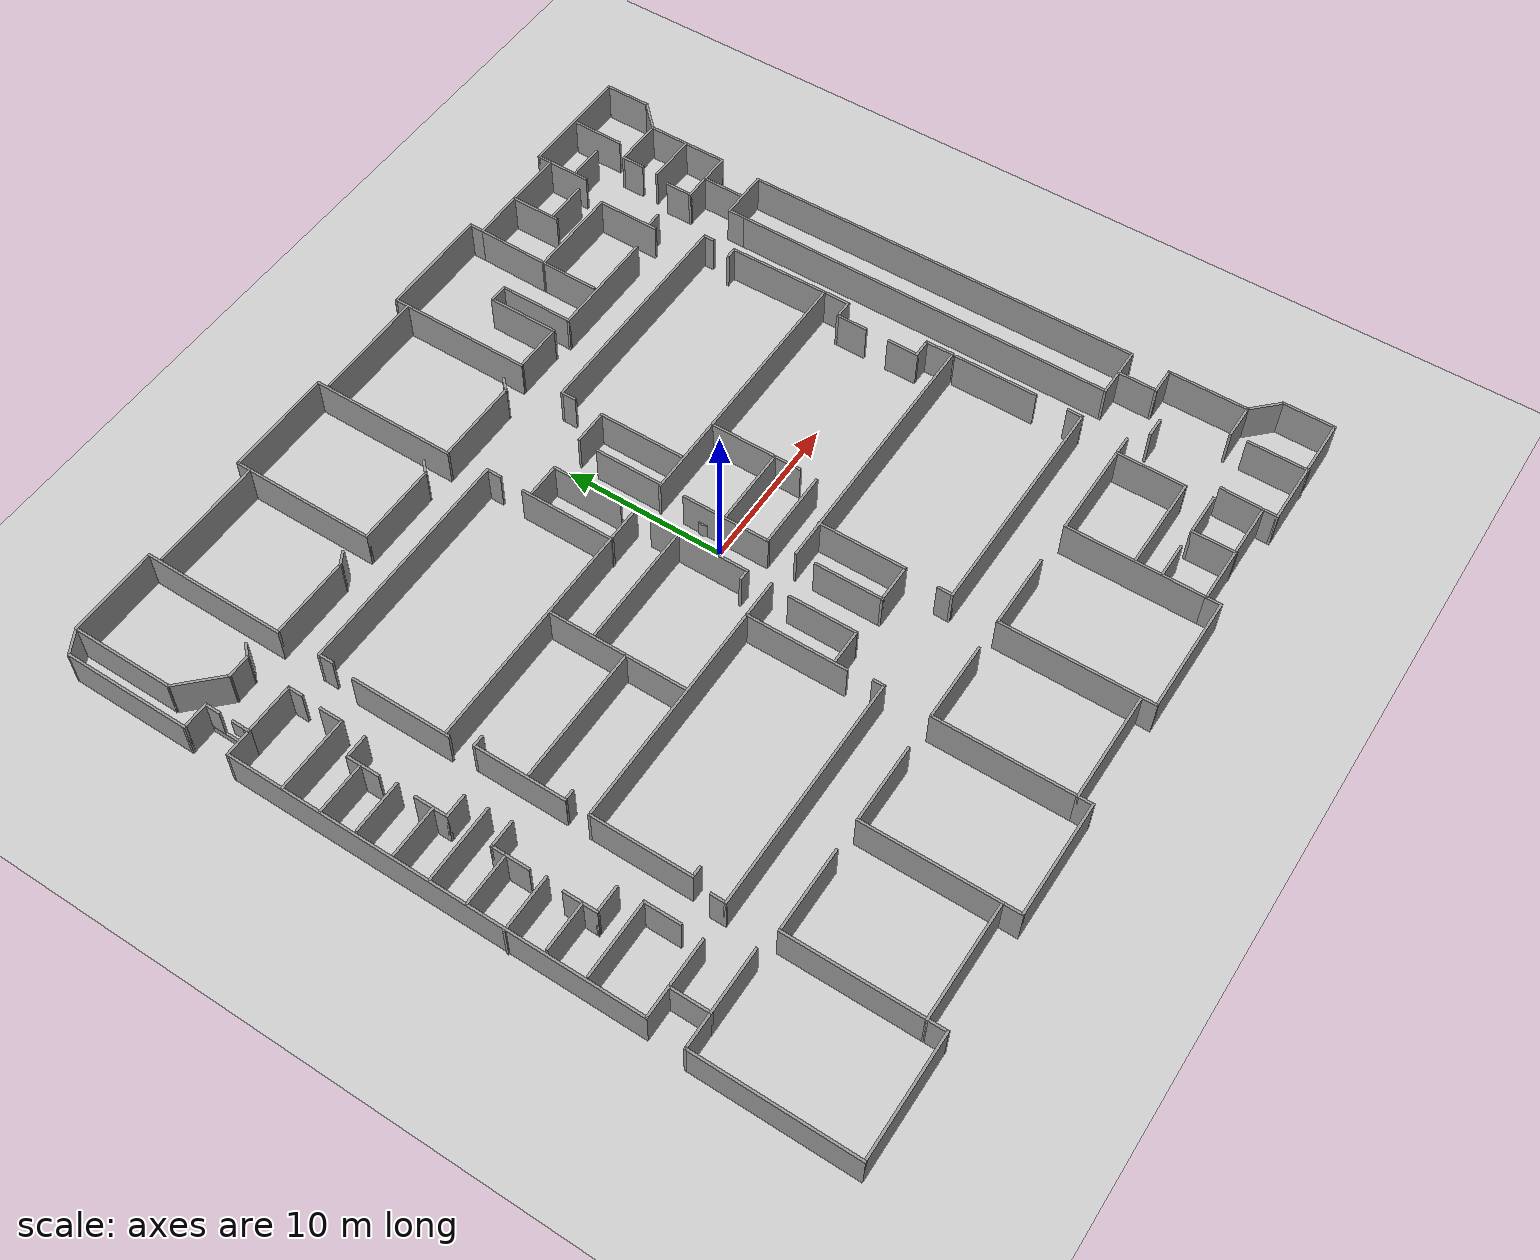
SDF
<sdf version='1.4'>
  <world name='default'>
    <!-- A global light source -->
    <include>
      <uri>model://sun</uri>
    </include>

    <!-- A ground plane -->
    <include>
      <uri>model://ground_plane</uri>
    </include>

    <physics type="ode">
      <real_time_update_rate>1000.0</real_time_update_rate>
      <max_step_size>0.001</max_step_size>
      <real_time_factor>1</real_time_factor>
      <ode>
        <solver>
          <type>quick</type>
          <iters>150</iters>
          <precon_iters>0</precon_iters>
          <sor>1.400000</sor>
          <use_dynamic_moi_rescaling>1</use_dynamic_moi_rescaling>
        </solver>
        <constraints>
          <cfm>0.00001</cfm>
          <erp>0.2</erp>
          <contact_max_correcting_vel>2000.000000</contact_max_correcting_vel>
          <contact_surface_layer>0.01000</contact_surface_layer>
        </constraints>
      </ode>
    </physics>

    <!-- Load world -->
    <include>
      <uri>model://KGCOE_MODEL</uri>
    </include>

    <model name='unit_cylinder'>
      <pose frame=''>0.990344 1.50775 0.5 0 -0 0</pose>
      <link name='link'>
        <inertial>
          <mass>1</mass>
          <inertia>
            <ixx>0.145833</ixx>
            <ixy>0</ixy>
            <ixz>0</ixz>
            <iyy>0.145833</iyy>
            <iyz>0</iyz>
            <izz>0.125</izz>
          </inertia>
        </inertial>
        <collision name='collision'>
          <geometry>
            <cylinder>
              <radius>0.5</radius>
              <length>1</length>
            </cylinder>
          </geometry>
          <max_contacts>10</max_contacts>
          <surface>
            <contact>
              <ode/>
            </contact>
            <bounce/>
            <friction>
              <torsional>
                <ode/>
              </torsional>
              <ode/>
            </friction>
          </surface>
        </collision>
        <visual name='visual'>
          <geometry>
            <cylinder>
              <radius>0.5</radius>
              <length>1</length>
            </cylinder>
          </geometry>
          <material>
            <script>
              <name>Gazebo/Grey</name>
              <uri>file://media/materials/scripts/gazebo.material</uri>
            </script>
          </material>
        </visual>
        <self_collide>0</self_collide>
        <enable_wind>0</enable_wind>
        <kinematic>0</kinematic>
      </link>
    </model>

    <scene>
      <ambient>0.4 0.4 0.4 1</ambient>
      <background>0.7 0.7 0.7 1</background>
      <shadows>true</shadows>
    </scene>

    <gui fullscreen='0'>
      <camera name='user_camera'>
        <pose>0.8 0.0 12.0 0 1.5708 0</pose>
        <view_controller>orbit</view_controller>
      </camera>
    </gui>
  </world>
</sdf>

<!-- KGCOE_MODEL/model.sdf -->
<sdf version='1.6'>
  <model name='Untitled'>
    <pose frame=''>-0.441057 -0.068194 0 0 -0 0</pose>
    <link name='Wall_268'>
      <collision name='Wall_268_Collision'>
        <geometry>
          <box>
            <size>1.75 0.15 2.5</size>
          </box>
        </geometry>
        <pose frame=''>0 0 1.25 0 -0 0</pose>
      </collision>
      <visual name='Wall_268_Visual'>
        <pose frame=''>0 0 1.25 0 -0 0</pose>
        <geometry>
          <box>
            <size>1.75 0.15 2.5</size>
          </box>
        </geometry>
        <material>
          <script>
            <uri>file://media/materials/scripts/gazebo.material</uri>
            <name>Gazebo/Grey</name>
          </script>
          <ambient>1 1 1 1</ambient>
        </material>
        <meta>
          <layer>0</layer>
        </meta>
      </visual>
      <pose frame=''>-23.9648 12.7736 0 0 -0 3.14159</pose>
    </link>
    <link name='Wall_269'>
      <collision name='Wall_269_Collision'>
        <geometry>
          <box>
            <size>25.5 0.15 2.5</size>
          </box>
        </geometry>
        <pose frame=''>0 0 1.25 0 -0 0</pose>
      </collision>
      <visual name='Wall_269_Visual'>
        <pose frame=''>0 0 1.25 0 -0 0</pose>
        <geometry>
          <box>
            <size>25.5 0.15 2.5</size>
          </box>
        </geometry>
        <material>
          <script>
            <uri>file://media/materials/scripts/gazebo.material</uri>
            <name>Gazebo/Grey</name>
          </script>
          <ambient>1 1 1 1</ambient>
        </material>
        <meta>
          <layer>0</layer>
        </meta>
      </visual>
      <pose frame=''>-24.7648 0.098619 0 0 -0 -1.5708</pose>
    </link>
    <link name='Wall_270'>
      <collision name='Wall_270_Collision'>
        <geometry>
          <box>
            <size>2 0.15 2.5</size>
          </box>
        </geometry>
        <pose frame=''>0 0 1.25 0 -0 0</pose>
      </collision>
      <visual name='Wall_270_Visual'>
        <pose frame=''>0 0 1.25 0 -0 0</pose>
        <geometry>
          <box>
            <size>2 0.15 2.5</size>
          </box>
        </geometry>
        <material>
          <script>
            <uri>file://media/materials/scripts/gazebo.material</uri>
            <name>Gazebo/Grey</name>
          </script>
          <ambient>1 1 1 1</ambient>
        </material>
        <meta>
          <layer>0</layer>
        </meta>
      </visual>
      <pose frame=''>-23.8398 -12.5764 0 0 -0 0</pose>
    </link>
    <link name='Wall_272'>
      <collision name='Wall_272_Collision'>
        <geometry>
          <box>
            <size>2.5 0.15 2.5</size>
          </box>
        </geometry>
        <pose frame=''>0 0 1.25 0 -0 0</pose>
      </collision>
      <visual name='Wall_272_Visual'>
        <pose frame=''>0 0 1.25 0 -0 0</pose>
        <geometry>
          <box>
            <size>2.5 0.15 2.5</size>
          </box>
        </geometry>
        <material>
          <script>
            <uri>file://media/materials/scripts/gazebo.material</uri>
            <name>Gazebo/Grey</name>
          </script>
          <ambient>1 1 1 1</ambient>
        </material>
        <meta>
          <layer>0</layer>
        </meta>
      </visual>
      <pose frame=''>-22.9148 -13.7514 0 0 -0 -1.5708</pose>
    </link>
    <link name='Wall_273'>
      <collision name='Wall_273_Collision'>
        <geometry>
          <box>
            <size>2.25 0.15 2.5</size>
          </box>
        </geometry>
        <pose frame=''>0 0 1.25 0 -0 0</pose>
      </collision>
      <visual name='Wall_273_Visual'>
        <pose frame=''>0 0 1.25 0 -0 0</pose>
        <geometry>
          <box>
            <size>2.25 0.15 2.5</size>
          </box>
        </geometry>
        <material>
          <script>
            <uri>file://media/materials/scripts/gazebo.material</uri>
            <name>Gazebo/Grey</name>
          </script>
          <ambient>1 1 1 1</ambient>
        </material>
        <meta>
          <layer>0</layer>
        </meta>
      </visual>
      <pose frame=''>-23.9648 -14.9264 0 0 -0 3.14159</pose>
    </link>
    <link name='Wall_274'>
      <collision name='Wall_274_Collision'>
        <geometry>
          <box>
            <size>9.75 0.15 2.5</size>
          </box>
        </geometry>
        <pose frame=''>0 0 1.25 0 -0 0</pose>
      </collision>
      <visual name='Wall_274_Visual'>
        <pose frame=''>0 0 1.25 0 -0 0</pose>
        <geometry>
          <box>
            <size>9.75 0.15 2.5</size>
          </box>
        </geometry>
        <material>
          <script>
            <uri>file://media/materials/scripts/gazebo.material</uri>
            <name>Gazebo/Grey</name>
          </script>
          <ambient>1 1 1 1</ambient>
        </material>
        <meta>
          <layer>0</layer>
        </meta>
      </visual>
      <pose frame=''>-25.0148 -19.7264 0 0 -0 -1.5708</pose>
    </link>
    <link name='Wall_276'>
      <collision name='Wall_276_Collision'>
        <geometry>
          <box>
            <size>7.5 0.15 2.5</size>
          </box>
        </geometry>
        <pose frame=''>0 0 1.25 0 -0 0</pose>
      </collision>
      <visual name='Wall_276_Visual'>
        <pose frame=''>0 0 1.25 0 -0 0</pose>
        <geometry>
          <box>
            <size>7.5 0.15 2.5</size>
          </box>
        </geometry>
        <material>
          <script>
            <uri>file://media/materials/scripts/gazebo.material</uri>
            <name>Gazebo/Grey</name>
          </script>
          <ambient>1 1 1 1</ambient>
        </material>
        <meta>
          <layer>0</layer>
        </meta>
      </visual>
      <pose frame=''>-21.3398 -24.5264 0 0 -0 0</pose>
    </link>
    <link name='Wall_277'>
      <collision name='Wall_277_Collision'>
        <geometry>
          <box>
            <size>1.25 0.15 2.5</size>
          </box>
        </geometry>
        <pose frame=''>0 0 1.25 0 -0 0</pose>
      </collision>
      <visual name='Wall_277_Visual'>
        <pose frame=''>0 0 1.25 0 -0 0</pose>
        <geometry>
          <box>
            <size>1.25 0.15 2.5</size>
          </box>
        </geometry>
        <material>
          <script>
            <uri>file://media/materials/scripts/gazebo.material</uri>
            <name>Gazebo/Grey</name>
          </script>
          <ambient>1 1 1 1</ambient>
        </material>
        <meta>
          <layer>0</layer>
        </meta>
      </visual>
      <pose frame=''>-17.6648 -23.9764 0 0 -0 1.5708</pose>
    </link>
    <link name='Wall_278'>
      <collision name='Wall_278_Collision'>
        <geometry>
          <box>
            <size>7.25 0.15 2.5</size>
          </box>
        </geometry>
        <pose frame=''>0 0 1.25 0 -0 0</pose>
      </collision>
      <visual name='Wall_278_Visual'>
        <pose frame=''>0 0 1.25 0 -0 0</pose>
        <geometry>
          <box>
            <size>7.25 0.15 2.5</size>
          </box>
        </geometry>
        <material>
          <script>
            <uri>file://media/materials/scripts/gazebo.material</uri>
            <name>Gazebo/Grey</name>
          </script>
          <ambient>1 1 1 1</ambient>
        </material>
        <meta>
          <layer>0</layer>
        </meta>
      </visual>
      <pose frame=''>-14.1148 -23.4264 0 0 -0 0</pose>
    </link>
    <link name='Wall_279'>
      <collision name='Wall_279_Collision'>
        <geometry>
          <box>
            <size>1.25 0.15 2.5</size>
          </box>
        </geometry>
        <pose frame=''>0 0 1.25 0 -0 0</pose>
      </collision>
      <visual name='Wall_279_Visual'>
        <pose frame=''>0 0 1.25 0 -0 0</pose>
        <geometry>
          <box>
            <size>1.25 0.15 2.5</size>
          </box>
        </geometry>
        <material>
          <script>
            <uri>file://media/materials/scripts/gazebo.material</uri>
            <name>Gazebo/Grey</name>
          </script>
          <ambient>1 1 1 1</ambient>
        </material>
        <meta>
          <layer>0</layer>
        </meta>
      </visual>
      <pose frame=''>-10.5648 -23.9764 0 0 -0 -1.5708</pose>
    </link>
    <link name='Wall_280'>
      <collision name='Wall_280_Collision'>
        <geometry>
          <box>
            <size>7.25 0.15 2.5</size>
          </box>
        </geometry>
        <pose frame=''>0 0 1.25 0 -0 0</pose>
      </collision>
      <visual name='Wall_280_Visual'>
        <pose frame=''>0 0 1.25 0 -0 0</pose>
        <geometry>
          <box>
            <size>7.25 0.15 2.5</size>
          </box>
        </geometry>
        <material>
          <script>
            <uri>file://media/materials/scripts/gazebo.material</uri>
            <name>Gazebo/Grey</name>
          </script>
          <ambient>1 1 1 1</ambient>
        </material>
        <meta>
          <layer>0</layer>
        </meta>
      </visual>
      <pose frame=''>-7.01479 -24.5264 0 0 -0 0</pose>
    </link>
    <link name='Wall_281'>
      <collision name='Wall_281_Collision'>
        <geometry>
          <box>
            <size>1 0.15 2.5</size>
          </box>
        </geometry>
        <pose frame=''>0 0 1.25 0 -0 0</pose>
      </collision>
      <visual name='Wall_281_Visual'>
        <pose frame=''>0 0 1.25 0 -0 0</pose>
        <geometry>
          <box>
            <size>1 0.15 2.5</size>
          </box>
        </geometry>
        <material>
          <script>
            <uri>file://media/materials/scripts/gazebo.material</uri>
            <name>Gazebo/Grey</name>
          </script>
          <ambient>1 1 1 1</ambient>
        </material>
        <meta>
          <layer>0</layer>
        </meta>
      </visual>
      <pose frame=''>-3.46479 -24.1014 0 0 -0 1.5708</pose>
    </link>
    <link name='Wall_282'>
      <collision name='Wall_282_Collision'>
        <geometry>
          <box>
            <size>7 0.15 2.5</size>
          </box>
        </geometry>
        <pose frame=''>0 0 1.25 0 -0 0</pose>
      </collision>
      <visual name='Wall_282_Visual'>
        <pose frame=''>0 0 1.25 0 -0 0</pose>
        <geometry>
          <box>
            <size>7 0.15 2.5</size>
          </box>
        </geometry>
        <material>
          <script>
            <uri>file://media/materials/scripts/gazebo.material</uri>
            <name>Gazebo/Grey</name>
          </script>
          <ambient>1 1 1 1</ambient>
        </material>
        <meta>
          <layer>0</layer>
        </meta>
      </visual>
      <pose frame=''>-0.039787 -23.6764 0 0 -0 0</pose>
    </link>
    <link name='Wall_283'>
      <collision name='Wall_283_Collision'>
        <geometry>
          <box>
            <size>1 0.15 2.5</size>
          </box>
        </geometry>
        <pose frame=''>0 0 1.25 0 -0 0</pose>
      </collision>
      <visual name='Wall_283_Visual'>
        <pose frame=''>0 0 1.25 0 -0 0</pose>
        <geometry>
          <box>
            <size>1 0.15 2.5</size>
          </box>
        </geometry>
        <material>
          <script>
            <uri>file://media/materials/scripts/gazebo.material</uri>
            <name>Gazebo/Grey</name>
          </script>
          <ambient>1 1 1 1</ambient>
        </material>
        <meta>
          <layer>0</layer>
        </meta>
      </visual>
      <pose frame=''>3.38521 -24.1014 0 0 -0 -1.5708</pose>
    </link>
    <link name='Wall_284'>
      <collision name='Wall_284_Collision'>
        <geometry>
          <box>
            <size>7.5 0.15 2.5</size>
          </box>
        </geometry>
        <pose frame=''>0 0 1.25 0 -0 0</pose>
      </collision>
      <visual name='Wall_284_Visual'>
        <pose frame=''>0 0 1.25 0 -0 0</pose>
        <geometry>
          <box>
            <size>7.5 0.15 2.5</size>
          </box>
        </geometry>
        <material>
          <script>
            <uri>file://media/materials/scripts/gazebo.material</uri>
            <name>Gazebo/Grey</name>
          </script>
          <ambient>1 1 1 1</ambient>
        </material>
        <meta>
          <layer>0</layer>
        </meta>
      </visual>
      <pose frame=''>7.06021 -24.5264 0 0 -0 0</pose>
    </link>
    <link name='Wall_285'>
      <collision name='Wall_285_Collision'>
        <geometry>
          <box>
            <size>1 0.15 2.5</size>
          </box>
        </geometry>
        <pose frame=''>0 0 1.25 0 -0 0</pose>
      </collision>
      <visual name='Wall_285_Visual'>
        <pose frame=''>0 0 1.25 0 -0 0</pose>
        <geometry>
          <box>
            <size>1 0.15 2.5</size>
          </box>
        </geometry>
        <material>
          <script>
            <uri>file://media/materials/scripts/gazebo.material</uri>
            <name>Gazebo/Grey</name>
          </script>
          <ambient>1 1 1 1</ambient>
        </material>
        <meta>
          <layer>0</layer>
        </meta>
      </visual>
      <pose frame=''>10.7352 -24.1014 0 0 -0 1.5708</pose>
    </link>
    <link name='Wall_287'>
      <collision name='Wall_287_Collision'>
        <geometry>
          <box>
            <size>7 0.15 2.5</size>
          </box>
        </geometry>
        <pose frame=''>0 0 1.25 0 -0 0</pose>
      </collision>
      <visual name='Wall_287_Visual'>
        <pose frame=''>0 0 1.25 0 -0 0</pose>
        <geometry>
          <box>
            <size>7 0.15 2.5</size>
          </box>
        </geometry>
        <material>
          <script>
            <uri>file://media/materials/scripts/gazebo.material</uri>
            <name>Gazebo/Grey</name>
          </script>
          <ambient>1 1 1 1</ambient>
        </material>
        <meta>
          <layer>0</layer>
        </meta>
      </visual>
      <pose frame=''>14.1602 -23.6764 0 0 -0 0</pose>
    </link>
    <link name='Wall_288'>
      <collision name='Wall_288_Collision'>
        <geometry>
          <box>
            <size>1 0.15 2.5</size>
          </box>
        </geometry>
        <pose frame=''>0 0 1.25 0 -0 0</pose>
      </collision>
      <visual name='Wall_288_Visual'>
        <pose frame=''>0 0 1.25 0 -0 0</pose>
        <geometry>
          <box>
            <size>1 0.15 2.5</size>
          </box>
        </geometry>
        <material>
          <script>
            <uri>file://media/materials/scripts/gazebo.material</uri>
            <name>Gazebo/Grey</name>
          </script>
          <ambient>1 1 1 1</ambient>
        </material>
        <meta>
          <layer>0</layer>
        </meta>
      </visual>
      <pose frame=''>17.5852 -24.1014 0 0 -0 -1.5708</pose>
    </link>
    <link name='Wall_289'>
      <collision name='Wall_289_Collision'>
        <geometry>
          <box>
            <size>7.5 0.15 2.5</size>
          </box>
        </geometry>
        <pose frame=''>0 0 1.25 0 -0 0</pose>
      </collision>
      <visual name='Wall_289_Visual'>
        <pose frame=''>0 0 1.25 0 -0 0</pose>
        <geometry>
          <box>
            <size>7.5 0.15 2.5</size>
          </box>
        </geometry>
        <material>
          <script>
            <uri>file://media/materials/scripts/gazebo.material</uri>
            <name>Gazebo/Grey</name>
          </script>
          <ambient>1 1 1 1</ambient>
        </material>
        <meta>
          <layer>0</layer>
        </meta>
      </visual>
      <pose frame=''>21.2602 -24.5264 0 0 -0 0</pose>
    </link>
    <link name='Wall_290'>
      <collision name='Wall_290_Collision'>
        <geometry>
          <box>
            <size>3.25 0.15 2.5</size>
          </box>
        </geometry>
        <pose frame=''>0 0 1.25 0 -0 0</pose>
      </collision>
      <visual name='Wall_290_Visual'>
        <pose frame=''>0 0 1.25 0 -0 0</pose>
        <geometry>
          <box>
            <size>3.25 0.15 2.5</size>
          </box>
        </geometry>
        <material>
          <script>
            <uri>file://media/materials/scripts/gazebo.material</uri>
            <name>Gazebo/Grey</name>
          </script>
          <ambient>1 1 1 1</ambient>
        </material>
        <meta>
          <layer>0</layer>
        </meta>
      </visual>
      <pose frame=''>24.9352 -22.9764 0 0 -0 1.5708</pose>
    </link>
    <link name='Wall_291'>
      <collision name='Wall_291_Collision'>
        <geometry>
          <box>
            <size>2.25 0.15 2.5</size>
          </box>
        </geometry>
        <pose frame=''>0 0 1.25 0 -0 0</pose>
      </collision>
      <visual name='Wall_291_Visual'>
        <pose frame=''>0 0 1.25 0 -0 0</pose>
        <geometry>
          <box>
            <size>2.25 0.15 2.5</size>
          </box>
        </geometry>
        <material>
          <script>
            <uri>file://media/materials/scripts/gazebo.material</uri>
            <name>Gazebo/Grey</name>
          </script>
          <ambient>1 1 1 1</ambient>
        </material>
        <meta>
          <layer>0</layer>
        </meta>
      </visual>
      <pose frame=''>24.1928 -20.6839 0 0 -0 2.35619</pose>
    </link>
    <link name='Wall_292'>
      <collision name='Wall_292_Collision'>
        <geometry>
          <box>
            <size>5 0.15 2.5</size>
          </box>
        </geometry>
        <pose frame=''>0 0 1.25 0 -0 0</pose>
      </collision>
      <visual name='Wall_292_Visual'>
        <pose frame=''>0 0 1.25 0 -0 0</pose>
        <geometry>
          <box>
            <size>5 0.15 2.5</size>
          </box>
        </geometry>
        <material>
          <script>
            <uri>file://media/materials/scripts/gazebo.material</uri>
            <name>Gazebo/Grey</name>
          </script>
          <ambient>1 1 1 1</ambient>
        </material>
        <meta>
          <layer>0</layer>
        </meta>
      </visual>
      <pose frame=''>23.4503 -17.5165 0 0 -0 1.5708</pose>
    </link>
    <link name='Wall_293'>
      <collision name='Wall_293_Collision'>
        <geometry>
          <box>
            <size>1.75 0.15 2.5</size>
          </box>
        </geometry>
        <pose frame=''>0 0 1.25 0 -0 0</pose>
      </collision>
      <visual name='Wall_293_Visual'>
        <pose frame=''>0 0 1.25 0 -0 0</pose>
        <geometry>
          <box>
            <size>1.75 0.15 2.5</size>
          </box>
        </geometry>
        <material>
          <script>
            <uri>file://media/materials/scripts/gazebo.material</uri>
            <name>Gazebo/Grey</name>
          </script>
          <ambient>1 1 1 1</ambient>
        </material>
        <meta>
          <layer>0</layer>
        </meta>
      </visual>
      <pose frame=''>22.6503 -15.0915 0 0 -0 3.14159</pose>
    </link>
    <link name='Wall_294'>
      <collision name='Wall_294_Collision'>
        <geometry>
          <box>
            <size>2.5 0.15 2.5</size>
          </box>
        </geometry>
        <pose frame=''>0 0 1.25 0 -0 0</pose>
      </collision>
      <visual name='Wall_294_Visual'>
        <pose frame=''>0 0 1.25 0 -0 0</pose>
        <geometry>
          <box>
            <size>2.5 0.15 2.5</size>
          </box>
        </geometry>
        <material>
          <script>
            <uri>file://media/materials/scripts/gazebo.material</uri>
            <name>Gazebo/Grey</name>
          </script>
          <ambient>1 1 1 1</ambient>
        </material>
        <meta>
          <layer>0</layer>
        </meta>
      </visual>
      <pose frame=''>21.8503 -13.9165 0 0 -0 1.5708</pose>
    </link>
    <link name='Wall_295'>
      <collision name='Wall_295_Collision'>
        <geometry>
          <box>
            <size>1.75 0.15 2.5</size>
          </box>
        </geometry>
        <pose frame=''>0 0 1.25 0 -0 0</pose>
      </collision>
      <visual name='Wall_295_Visual'>
        <pose frame=''>0 0 1.25 0 -0 0</pose>
        <geometry>
          <box>
            <size>1.75 0.15 2.5</size>
          </box>
        </geometry>
        <material>
          <script>
            <uri>file://media/materials/scripts/gazebo.material</uri>
            <name>Gazebo/Grey</name>
          </script>
          <ambient>1 1 1 1</ambient>
        </material>
        <meta>
          <layer>0</layer>
        </meta>
      </visual>
      <pose frame=''>22.6503 -12.7415 0 0 -0 0</pose>
    </link>
    <link name='Wall_298'>
      <collision name='Wall_298_Collision'>
        <geometry>
          <box>
            <size>8.5 0.15 2.5</size>
          </box>
        </geometry>
        <pose frame=''>0 0 1.25 0 -0 0</pose>
      </collision>
      <visual name='Wall_298_Visual'>
        <pose frame=''>0 0 1.25 0 -0 0</pose>
        <geometry>
          <box>
            <size>8.5 0.15 2.5</size>
          </box>
        </geometry>
        <material>
          <script>
            <uri>file://media/materials/scripts/gazebo.material</uri>
            <name>Gazebo/Grey</name>
          </script>
          <ambient>1 1 1 1</ambient>
        </material>
        <meta>
          <layer>0</layer>
        </meta>
      </visual>
      <pose frame=''>10.7352 -19.5014 0 0 -0 1.5708</pose>
    </link>
    <link name='Wall_299'>
      <collision name='Wall_299_Collision'>
        <geometry>
          <box>
            <size>7.25 0.15 2.5</size>
          </box>
        </geometry>
        <pose frame=''>0 0 1.25 0 -0 0</pose>
      </collision>
      <visual name='Wall_299_Visual'>
        <pose frame=''>0 0 1.25 0 -0 0</pose>
        <geometry>
          <box>
            <size>7.25 0.15 2.5</size>
          </box>
        </geometry>
        <material>
          <script>
            <uri>file://media/materials/scripts/gazebo.material</uri>
            <name>Gazebo/Grey</name>
          </script>
          <ambient>1 1 1 1</ambient>
        </material>
        <meta>
          <layer>0</layer>
        </meta>
      </visual>
      <pose frame=''>14.2852 -15.3264 0 0 -0 0</pose>
    </link>
    <link name='Wall_301'>
      <collision name='Wall_301_Collision'>
        <geometry>
          <box>
            <size>6 0.15 2.5</size>
          </box>
        </geometry>
        <pose frame=''>0 0 1.25 0 -0 0</pose>
      </collision>
      <visual name='Wall_301_Visual'>
        <pose frame=''>0 0 1.25 0 -0 0</pose>
        <geometry>
          <box>
            <size>6 0.15 2.5</size>
          </box>
        </geometry>
        <material>
          <script>
            <uri>file://media/materials/scripts/gazebo.material</uri>
            <name>Gazebo/Grey</name>
          </script>
          <ambient>1 1 1 1</ambient>
        </material>
        <meta>
          <layer>0</layer>
        </meta>
      </visual>
      <pose frame=''>13.7673 -19.4861 0 0 -0 0</pose>
    </link>
    <link name='Wall_302'>
      <collision name='Wall_302_Collision'>
        <geometry>
          <box>
            <size>4.25 0.15 2.5</size>
          </box>
        </geometry>
        <pose frame=''>0 0 1.25 0 -0 0</pose>
      </collision>
      <visual name='Wall_302_Visual'>
        <pose frame=''>0 0 1.25 0 -0 0</pose>
        <geometry>
          <box>
            <size>4.25 0.15 2.5</size>
          </box>
        </geometry>
        <material>
          <script>
            <uri>file://media/materials/scripts/gazebo.material</uri>
            <name>Gazebo/Grey</name>
          </script>
          <ambient>1 1 1 1</ambient>
        </material>
        <meta>
          <layer>0</layer>
        </meta>
      </visual>
      <pose frame=''>16.6923 -17.4361 0 0 -0 1.5708</pose>
    </link>
    <link name='Wall_304'>
      <collision name='Wall_304_Collision'>
        <geometry>
          <box>
            <size>2.75 0.15 2.5</size>
          </box>
        </geometry>
        <pose frame=''>0 0 1.25 0 -0 0</pose>
      </collision>
      <visual name='Wall_304_Visual'>
        <pose frame=''>0 0 1.25 0 -0 0</pose>
        <geometry>
          <box>
            <size>2.75 0.15 2.5</size>
          </box>
        </geometry>
        <material>
          <script>
            <uri>file://media/materials/scripts/gazebo.material</uri>
            <name>Gazebo/Grey</name>
          </script>
          <ambient>1 1 1 1</ambient>
        </material>
        <meta>
          <layer>0</layer>
        </meta>
      </visual>
      <pose frame=''>14.1825 -22.4168 0 0 -0 -1.5708</pose>
    </link>
    <link name='Wall_306'>
      <collision name='Wall_306_Collision'>
        <geometry>
          <box>
            <size>2.25 0.15 2.5</size>
          </box>
        </geometry>
        <pose frame=''>0 0 1.25 0 -0 0</pose>
      </collision>
      <visual name='Wall_306_Visual'>
        <pose frame=''>0 0 1.25 0 -0 0</pose>
        <geometry>
          <box>
            <size>2.25 0.15 2.5</size>
          </box>
        </geometry>
        <material>
          <script>
            <uri>file://media/materials/scripts/gazebo.material</uri>
            <name>Gazebo/Grey</name>
          </script>
          <ambient>1 1 1 1</ambient>
        </material>
        <meta>
          <layer>0</layer>
        </meta>
      </visual>
      <pose frame=''>11.8923 -21.0905 0 0 -0 0</pose>
    </link>
    <link name='Wall_308'>
      <collision name='Wall_308_Collision'>
        <geometry>
          <box>
            <size>2.75 0.15 2.5</size>
          </box>
        </geometry>
        <pose frame=''>0 0 1.25 0 -0 0</pose>
      </collision>
      <visual name='Wall_308_Visual'>
        <pose frame=''>0 0 1.25 0 -0 0</pose>
        <geometry>
          <box>
            <size>2.75 0.15 2.5</size>
          </box>
        </geometry>
        <material>
          <script>
            <uri>file://media/materials/scripts/gazebo.material</uri>
            <name>Gazebo/Grey</name>
          </script>
          <ambient>1 1 1 1</ambient>
        </material>
        <meta>
          <layer>0</layer>
        </meta>
      </visual>
      <pose frame=''>15.4825 -21.1168 0 0 -0 0</pose>
    </link>
    <link name='Wall_310'>
      <collision name='Wall_310_Collision'>
        <geometry>
          <box>
            <size>2.68425 0.15 2.5</size>
          </box>
        </geometry>
        <pose frame=''>0 0 1.25 0 -0 0</pose>
      </collision>
      <visual name='Wall_310_Visual'>
        <pose frame=''>0 0 1.25 0 -0 0</pose>
        <geometry>
          <box>
            <size>2.68425 0.15 2.5</size>
          </box>
        </geometry>
        <material>
          <script>
            <uri>file://media/materials/scripts/gazebo.material</uri>
            <name>Gazebo/Grey</name>
          </script>
          <ambient>1 1 1 1</ambient>
        </material>
        <meta>
          <layer>0</layer>
        </meta>
      </visual>
      <pose frame=''>17.6197 -22.4097 0 0 -0 -1.59801</pose>
    </link>
    <link name='Wall_312'>
      <collision name='Wall_312_Collision'>
        <geometry>
          <box>
            <size>3.75 0.15 2.5</size>
          </box>
        </geometry>
        <pose frame=''>0 0 1.25 0 -0 0</pose>
      </collision>
      <visual name='Wall_312_Visual'>
        <pose frame=''>0 0 1.25 0 -0 0</pose>
        <geometry>
          <box>
            <size>3.75 0.15 2.5</size>
          </box>
        </geometry>
        <material>
          <script>
            <uri>file://media/materials/scripts/gazebo.material</uri>
            <name>Gazebo/Grey</name>
          </script>
          <ambient>1 1 1 1</ambient>
        </material>
        <meta>
          <layer>0</layer>
        </meta>
      </visual>
      <pose frame=''>21.3626 -22.7853 0 0 -0 -1.5708</pose>
    </link>
    <link name='Wall_314'>
      <collision name='Wall_314_Collision'>
        <geometry>
          <box>
            <size>2.25 0.15 2.5</size>
          </box>
        </geometry>
        <pose frame=''>0 0 1.25 0 -0 0</pose>
      </collision>
      <visual name='Wall_314_Visual'>
        <pose frame=''>0 0 1.25 0 -0 0</pose>
        <geometry>
          <box>
            <size>2.25 0.15 2.5</size>
          </box>
        </geometry>
        <material>
          <script>
            <uri>file://media/materials/scripts/gazebo.material</uri>
            <name>Gazebo/Grey</name>
          </script>
          <ambient>1 1 1 1</ambient>
        </material>
        <meta>
          <layer>0</layer>
        </meta>
      </visual>
      <pose frame=''>22.4003 -19.9415 0 0 -0 3.14159</pose>
    </link>
    <link name='Wall_316'>
      <collision name='Wall_316_Collision'>
        <geometry>
          <box>
            <size>1.25 0.15 2.5</size>
          </box>
        </geometry>
        <pose frame=''>0 0 1.25 0 -0 0</pose>
      </collision>
      <visual name='Wall_316_Visual'>
        <pose frame=''>0 0 1.25 0 -0 0</pose>
        <geometry>
          <box>
            <size>1.25 0.15 2.5</size>
          </box>
        </geometry>
        <material>
          <script>
            <uri>file://media/materials/scripts/gazebo.material</uri>
            <name>Gazebo/Grey</name>
          </script>
          <ambient>1 1 1 1</ambient>
        </material>
        <meta>
          <layer>0</layer>
        </meta>
      </visual>
      <pose frame=''>19.4666 -16.2511 0 0 -0 0</pose>
    </link>
    <link name='Wall_318'>
      <collision name='Wall_318_Collision'>
        <geometry>
          <box>
            <size>1 0.15 2.5</size>
          </box>
        </geometry>
        <pose frame=''>0 0 1.25 0 -0 0</pose>
      </collision>
      <visual name='Wall_318_Visual'>
        <pose frame=''>0 0 1.25 0 -0 0</pose>
        <geometry>
          <box>
            <size>1 0.15 2.5</size>
          </box>
        </geometry>
        <material>
          <script>
            <uri>file://media/materials/scripts/gazebo.material</uri>
            <name>Gazebo/Grey</name>
          </script>
          <ambient>1 1 1 1</ambient>
        </material>
        <meta>
          <layer>0</layer>
        </meta>
      </visual>
      <pose frame=''>3.53073 -12.0998 0 0 -0 -1.5708</pose>
    </link>
    <link name='Wall_319'>
      <collision name='Wall_319_Collision'>
        <geometry>
          <box>
            <size>14.5 0.15 2.5</size>
          </box>
        </geometry>
        <pose frame=''>0 0 1.25 0 -0 0</pose>
      </collision>
      <visual name='Wall_319_Visual'>
        <pose frame=''>0 0 1.25 0 -0 0</pose>
        <geometry>
          <box>
            <size>14.5 0.15 2.5</size>
          </box>
        </geometry>
        <material>
          <script>
            <uri>file://media/materials/scripts/gazebo.material</uri>
            <name>Gazebo/Grey</name>
          </script>
          <ambient>1 1 1 1</ambient>
        </material>
        <meta>
          <layer>0</layer>
        </meta>
      </visual>
      <pose frame=''>10.7057 -12.5248 0 0 -0 0</pose>
    </link>
    <link name='Wall_320'>
      <collision name='Wall_320_Collision'>
        <geometry>
          <box>
            <size>1 0.15 2.5</size>
          </box>
        </geometry>
        <pose frame=''>0 0 1.25 0 -0 0</pose>
      </collision>
      <visual name='Wall_320_Visual'>
        <pose frame=''>0 0 1.25 0 -0 0</pose>
        <geometry>
          <box>
            <size>1 0.15 2.5</size>
          </box>
        </geometry>
        <material>
          <script>
            <uri>file://media/materials/scripts/gazebo.material</uri>
            <name>Gazebo/Grey</name>
          </script>
          <ambient>1 1 1 1</ambient>
        </material>
        <meta>
          <layer>0</layer>
        </meta>
      </visual>
      <pose frame=''>17.8807 -12.0998 0 0 -0 1.5708</pose>
    </link>
    <link name='Wall_322'>
      <collision name='Wall_322_Collision'>
        <geometry>
          <box>
            <size>4.75 0.15 2.5</size>
          </box>
        </geometry>
        <pose frame=''>0 0 1.25 0 -0 0</pose>
      </collision>
      <visual name='Wall_322_Visual'>
        <pose frame=''>0 0 1.25 0 -0 0</pose>
        <geometry>
          <box>
            <size>4.75 0.15 2.5</size>
          </box>
        </geometry>
        <material>
          <script>
            <uri>file://media/materials/scripts/gazebo.material</uri>
            <name>Gazebo/Grey</name>
          </script>
          <ambient>1 1 1 1</ambient>
        </material>
        <meta>
          <layer>0</layer>
        </meta>
      </visual>
      <pose frame=''>5.72553 -15.3306 0 0 -0 0</pose>
    </link>
    <link name='Wall_325'>
      <collision name='Wall_325_Collision'>
        <geometry>
          <box>
            <size>8.5 0.15 2.5</size>
          </box>
        </geometry>
        <pose frame=''>0 0 1.25 0 -0 0</pose>
      </collision>
      <visual name='Wall_325_Visual'>
        <pose frame=''>0 0 1.25 0 -0 0</pose>
        <geometry>
          <box>
            <size>8.5 0.15 2.5</size>
          </box>
        </geometry>
        <material>
          <script>
            <uri>file://media/materials/scripts/gazebo.material</uri>
            <name>Gazebo/Grey</name>
          </script>
          <ambient>1 1 1 1</ambient>
        </material>
        <meta>
          <layer>0</layer>
        </meta>
      </visual>
      <pose frame=''>3.38521 -19.5014 0 0 -0 1.5708</pose>
    </link>
    <link name='Wall_327'>
      <collision name='Wall_327_Collision'>
        <geometry>
          <box>
            <size>8.5 0.15 2.5</size>
          </box>
        </geometry>
        <pose frame=''>0 0 1.25 0 -0 0</pose>
      </collision>
      <visual name='Wall_327_Visual'>
        <pose frame=''>0 0 1.25 0 -0 0</pose>
        <geometry>
          <box>
            <size>8.5 0.15 2.5</size>
          </box>
        </geometry>
        <material>
          <script>
            <uri>file://media/materials/scripts/gazebo.material</uri>
            <name>Gazebo/Grey</name>
          </script>
          <ambient>1 1 1 1</ambient>
        </material>
        <meta>
          <layer>0</layer>
        </meta>
      </visual>
      <pose frame=''>-3.46479 -19.5014 0 0 -0 1.5708</pose>
    </link>
    <link name='Wall_328'>
      <collision name='Wall_328_Collision'>
        <geometry>
          <box>
            <size>5 0.15 2.5</size>
          </box>
        </geometry>
        <pose frame=''>0 0 1.25 0 -0 0</pose>
      </collision>
      <visual name='Wall_328_Visual'>
        <pose frame=''>0 0 1.25 0 -0 0</pose>
        <geometry>
          <box>
            <size>5 0.15 2.5</size>
          </box>
        </geometry>
        <material>
          <script>
            <uri>file://media/materials/scripts/gazebo.material</uri>
            <name>Gazebo/Grey</name>
          </script>
          <ambient>1 1 1 1</ambient>
        </material>
        <meta>
          <layer>0</layer>
        </meta>
      </visual>
      <pose frame=''>-1.03979 -15.3264 0 0 -0 0</pose>
    </link>
    <link name='Wall_330'>
      <collision name='Wall_330_Collision'>
        <geometry>
          <box>
            <size>8.25 0.15 2.5</size>
          </box>
        </geometry>
        <pose frame=''>0 0 1.25 0 -0 0</pose>
      </collision>
      <visual name='Wall_330_Visual'>
        <pose frame=''>0 0 1.25 0 -0 0</pose>
        <geometry>
          <box>
            <size>8.25 0.15 2.5</size>
          </box>
        </geometry>
        <material>
          <script>
            <uri>file://media/materials/scripts/gazebo.material</uri>
            <name>Gazebo/Grey</name>
          </script>
          <ambient>1 1 1 1</ambient>
        </material>
        <meta>
          <layer>0</layer>
        </meta>
      </visual>
      <pose frame=''>-10.5648 -19.3764 0 0 -0 1.5708</pose>
    </link>
    <link name='Wall_331'>
      <collision name='Wall_331_Collision'>
        <geometry>
          <box>
            <size>5 0.15 2.5</size>
          </box>
        </geometry>
        <pose frame=''>0 0 1.25 0 -0 0</pose>
      </collision>
      <visual name='Wall_331_Visual'>
        <pose frame=''>0 0 1.25 0 -0 0</pose>
        <geometry>
          <box>
            <size>5 0.15 2.5</size>
          </box>
        </geometry>
        <material>
          <script>
            <uri>file://media/materials/scripts/gazebo.material</uri>
            <name>Gazebo/Grey</name>
          </script>
          <ambient>1 1 1 1</ambient>
        </material>
        <meta>
          <layer>0</layer>
        </meta>
      </visual>
      <pose frame=''>-8.13979 -15.3264 0 0 -0 0</pose>
    </link>
    <link name='Wall_333'>
      <collision name='Wall_333_Collision'>
        <geometry>
          <box>
            <size>8.25 0.15 2.5</size>
          </box>
        </geometry>
        <pose frame=''>0 0 1.25 0 -0 0</pose>
      </collision>
      <visual name='Wall_333_Visual'>
        <pose frame=''>0 0 1.25 0 -0 0</pose>
        <geometry>
          <box>
            <size>8.25 0.15 2.5</size>
          </box>
        </geometry>
        <material>
          <script>
            <uri>file://media/materials/scripts/gazebo.material</uri>
            <name>Gazebo/Grey</name>
          </script>
          <ambient>1 1 1 1</ambient>
        </material>
        <meta>
          <layer>0</layer>
        </meta>
      </visual>
      <pose frame=''>-17.6648 -19.3764 0 0 -0 1.5708</pose>
    </link>
    <link name='Wall_334'>
      <collision name='Wall_334_Collision'>
        <geometry>
          <box>
            <size>5.25 0.15 2.5</size>
          </box>
        </geometry>
        <pose frame=''>0 0 1.25 0 -0 0</pose>
      </collision>
      <visual name='Wall_334_Visual'>
        <pose frame=''>0 0 1.25 0 -0 0</pose>
        <geometry>
          <box>
            <size>5.25 0.15 2.5</size>
          </box>
        </geometry>
        <material>
          <script>
            <uri>file://media/materials/scripts/gazebo.material</uri>
            <name>Gazebo/Grey</name>
          </script>
          <ambient>1 1 1 1</ambient>
        </material>
        <meta>
          <layer>0</layer>
        </meta>
      </visual>
      <pose frame=''>-15.1148 -15.3264 0 0 -0 0</pose>
    </link>
    <link name='Wall_336'>
      <collision name='Wall_336_Collision'>
        <geometry>
          <box>
            <size>4 0.15 2.5</size>
          </box>
        </geometry>
        <pose frame=''>0 0 1.25 0 -0 0</pose>
      </collision>
      <visual name='Wall_336_Visual'>
        <pose frame=''>0 0 1.25 0 -0 0</pose>
        <geometry>
          <box>
            <size>4 0.15 2.5</size>
          </box>
        </geometry>
        <material>
          <script>
            <uri>file://media/materials/scripts/gazebo.material</uri>
            <name>Gazebo/Grey</name>
          </script>
          <ambient>1 1 1 1</ambient>
        </material>
        <meta>
          <layer>0</layer>
        </meta>
      </visual>
      <pose frame=''>-20.9898 -14.9264 0 0 -0 0</pose>
    </link>
    <link name='Wall_338'>
      <collision name='Wall_338_Collision'>
        <geometry>
          <box>
            <size>1.75 0.15 2.5</size>
          </box>
        </geometry>
        <pose frame=''>0 0 1.25 0 -0 0</pose>
      </collision>
      <visual name='Wall_338_Visual'>
        <pose frame=''>0 0 1.25 0 -0 0</pose>
        <geometry>
          <box>
            <size>1.75 0.15 2.5</size>
          </box>
        </geometry>
        <material>
          <script>
            <uri>file://media/materials/scripts/gazebo.material</uri>
            <name>Gazebo/Grey</name>
          </script>
          <ambient>1 1 1 1</ambient>
        </material>
        <meta>
          <layer>0</layer>
        </meta>
      </visual>
      <pose frame=''>21.0503 -12.7415 0 0 -0 3.14159</pose>
    </link>
    <link name='Wall_339'>
      <collision name='Wall_339_Collision'>
        <geometry>
          <box>
            <size>24.25 0.15 2.5</size>
          </box>
        </geometry>
        <pose frame=''>0 0 1.25 0 -0 0</pose>
      </collision>
      <visual name='Wall_339_Visual'>
        <pose frame=''>0 0 1.25 0 -0 0</pose>
        <geometry>
          <box>
            <size>24.25 0.15 2.5</size>
          </box>
        </geometry>
        <material>
          <script>
            <uri>file://media/materials/scripts/gazebo.material</uri>
            <name>Gazebo/Grey</name>
          </script>
          <ambient>1 1 1 1</ambient>
        </material>
        <meta>
          <layer>0</layer>
        </meta>
      </visual>
      <pose frame=''>20.2503 -0.691456 0 0 -0 1.5708</pose>
    </link>
    <link name='Wall_342'>
      <collision name='Wall_342_Collision'>
        <geometry>
          <box>
            <size>1.25 0.15 2.5</size>
          </box>
        </geometry>
        <pose frame=''>0 0 1.25 0 -0 0</pose>
      </collision>
      <visual name='Wall_342_Visual'>
        <pose frame=''>0 0 1.25 0 -0 0</pose>
        <geometry>
          <box>
            <size>1.25 0.15 2.5</size>
          </box>
        </geometry>
        <material>
          <script>
            <uri>file://media/materials/scripts/gazebo.material</uri>
            <name>Gazebo/Grey</name>
          </script>
          <ambient>1 1 1 1</ambient>
        </material>
        <meta>
          <layer>0</layer>
        </meta>
      </visual>
      <pose frame=''>20.2503 11.9085 0 0 -0 1.5708</pose>
    </link>
    <link name='Wall_343'>
      <collision name='Wall_343_Collision'>
        <geometry>
          <box>
            <size>3.25 0.15 2.5</size>
          </box>
        </geometry>
        <pose frame=''>0 0 1.25 0 -0 0</pose>
      </collision>
      <visual name='Wall_343_Visual'>
        <pose frame=''>0 0 1.25 0 -0 0</pose>
        <geometry>
          <box>
            <size>3.25 0.15 2.5</size>
          </box>
        </geometry>
        <material>
          <script>
            <uri>file://media/materials/scripts/gazebo.material</uri>
            <name>Gazebo/Grey</name>
          </script>
          <ambient>1 1 1 1</ambient>
        </material>
        <meta>
          <layer>0</layer>
        </meta>
      </visual>
      <pose frame=''>21.8003 12.4585 0 0 -0 0</pose>
    </link>
    <link name='Wall_344'>
      <collision name='Wall_344_Collision'>
        <geometry>
          <box>
            <size>25.3502 0.15 2.5</size>
          </box>
        </geometry>
        <pose frame=''>0 0 1.25 0 -0 0</pose>
      </collision>
      <visual name='Wall_344_Visual'>
        <pose frame=''>0 0 1.25 0 -0 0</pose>
        <geometry>
          <box>
            <size>25.3502 0.15 2.5</size>
          </box>
        </geometry>
        <material>
          <script>
            <uri>file://media/materials/scripts/gazebo.material</uri>
            <name>Gazebo/Grey</name>
          </script>
          <ambient>1 1 1 1</ambient>
        </material>
        <meta>
          <layer>0</layer>
        </meta>
      </visual>
      <pose frame=''>23.4003 -0.141456 0 0 -0 -1.56683</pose>
    </link>
    <link name='Wall_346'>
      <collision name='Wall_346_Collision'>
        <geometry>
          <box>
            <size>1 0.15 2.5</size>
          </box>
        </geometry>
        <pose frame=''>0 0 1.25 0 -0 0</pose>
      </collision>
      <visual name='Wall_346_Visual'>
        <pose frame=''>0 0 1.25 0 -0 0</pose>
        <geometry>
          <box>
            <size>1 0.15 2.5</size>
          </box>
        </geometry>
        <material>
          <script>
            <uri>file://media/materials/scripts/gazebo.material</uri>
            <name>Gazebo/Grey</name>
          </script>
          <ambient>1 1 1 1</ambient>
        </material>
        <meta>
          <layer>0</layer>
        </meta>
      </visual>
      <pose frame=''>-17.8511 -11.9941 0 0 -0 -1.5708</pose>
    </link>
    <link name='Wall_347'>
      <collision name='Wall_347_Collision'>
        <geometry>
          <box>
            <size>14.75 0.15 2.5</size>
          </box>
        </geometry>
        <pose frame=''>0 0 1.25 0 -0 0</pose>
      </collision>
      <visual name='Wall_347_Visual'>
        <pose frame=''>0 0 1.25 0 -0 0</pose>
        <geometry>
          <box>
            <size>14.75 0.15 2.5</size>
          </box>
        </geometry>
        <material>
          <script>
            <uri>file://media/materials/scripts/gazebo.material</uri>
            <name>Gazebo/Grey</name>
          </script>
          <ambient>1 1 1 1</ambient>
        </material>
        <meta>
          <layer>0</layer>
        </meta>
      </visual>
      <pose frame=''>-10.5511 -12.4191 0 0 -0 0</pose>
    </link>
    <link name='Wall_348'>
      <collision name='Wall_348_Collision'>
        <geometry>
          <box>
            <size>0.75 0.15 2.5</size>
          </box>
        </geometry>
        <pose frame=''>0 0 1.25 0 -0 0</pose>
      </collision>
      <visual name='Wall_348_Visual'>
        <pose frame=''>0 0 1.25 0 -0 0</pose>
        <geometry>
          <box>
            <size>0.75 0.15 2.5</size>
          </box>
        </geometry>
        <material>
          <script>
            <uri>file://media/materials/scripts/gazebo.material</uri>
            <name>Gazebo/Grey</name>
          </script>
          <ambient>1 1 1 1</ambient>
        </material>
        <meta>
          <layer>0</layer>
        </meta>
      </visual>
      <pose frame=''>-3.25106 -12.1191 0 0 -0 1.5708</pose>
    </link>
    <link name='Wall_350'>
      <collision name='Wall_350_Collision'>
        <geometry>
          <box>
            <size>3 0.15 2.5</size>
          </box>
        </geometry>
        <pose frame=''>0 0 1.25 0 -0 0</pose>
      </collision>
      <visual name='Wall_350_Visual'>
        <pose frame=''>0 0 1.25 0 -0 0</pose>
        <geometry>
          <box>
            <size>3 0.15 2.5</size>
          </box>
        </geometry>
        <material>
          <script>
            <uri>file://media/materials/scripts/gazebo.material</uri>
            <name>Gazebo/Grey</name>
          </script>
          <ambient>1 1 1 1</ambient>
        </material>
        <meta>
          <layer>0</layer>
        </meta>
      </visual>
      <pose frame=''>-21.4898 -12.5764 0 0 -0 0</pose>
    </link>
    <link name='Wall_352'>
      <collision name='Wall_352_Collision'>
        <geometry>
          <box>
            <size>4.75 0.15 2.5</size>
          </box>
        </geometry>
        <pose frame=''>0 0 1.25 0 -0 0</pose>
      </collision>
      <visual name='Wall_352_Visual'>
        <pose frame=''>0 0 1.25 0 -0 0</pose>
        <geometry>
          <box>
            <size>4.75 0.15 2.5</size>
          </box>
        </geometry>
        <material>
          <script>
            <uri>file://media/materials/scripts/gazebo.material</uri>
            <name>Gazebo/Grey</name>
          </script>
          <ambient>1 1 1 1</ambient>
        </material>
        <meta>
          <layer>0</layer>
        </meta>
      </visual>
      <pose frame=''>-22.2641 -9.1343 0 0 -0 0</pose>
    </link>
    <link name='Wall_353'>
      <collision name='Wall_353_Collision'>
        <geometry>
          <box>
            <size>2.25 0.15 2.5</size>
          </box>
        </geometry>
        <pose frame=''>0 0 1.25 0 -0 0</pose>
      </collision>
      <visual name='Wall_353_Visual'>
        <pose frame=''>0 0 1.25 0 -0 0</pose>
        <geometry>
          <box>
            <size>2.25 0.15 2.5</size>
          </box>
        </geometry>
        <material>
          <script>
            <uri>file://media/materials/scripts/gazebo.material</uri>
            <name>Gazebo/Grey</name>
          </script>
          <ambient>1 1 1 1</ambient>
        </material>
        <meta>
          <layer>0</layer>
        </meta>
      </visual>
      <pose frame=''>-19.9641 -10.1843 0 0 -0 -1.5708</pose>
    </link>
    <link name='Wall_355'>
      <collision name='Wall_355_Collision'>
        <geometry>
          <box>
            <size>3 0.15 2.5</size>
          </box>
        </geometry>
        <pose frame=''>0 0 1.25 0 -0 0</pose>
      </collision>
      <visual name='Wall_355_Visual'>
        <pose frame=''>0 0 1.25 0 -0 0</pose>
        <geometry>
          <box>
            <size>3 0.15 2.5</size>
          </box>
        </geometry>
        <material>
          <script>
            <uri>file://media/materials/scripts/gazebo.material</uri>
            <name>Gazebo/Grey</name>
          </script>
          <ambient>1 1 1 1</ambient>
        </material>
        <meta>
          <layer>0</layer>
        </meta>
      </visual>
      <pose frame=''>-23.0695 -6.7343 0 0 -0 0</pose>
    </link>
    <link name='Wall_356'>
      <collision name='Wall_356_Collision'>
        <geometry>
          <box>
            <size>1.25 0.15 2.5</size>
          </box>
        </geometry>
        <pose frame=''>0 0 1.25 0 -0 0</pose>
      </collision>
      <visual name='Wall_356_Visual'>
        <pose frame=''>0 0 1.25 0 -0 0</pose>
        <geometry>
          <box>
            <size>1.25 0.15 2.5</size>
          </box>
        </geometry>
        <material>
          <script>
            <uri>file://media/materials/scripts/gazebo.material</uri>
            <name>Gazebo/Grey</name>
          </script>
          <ambient>1 1 1 1</ambient>
        </material>
        <meta>
          <layer>0</layer>
        </meta>
      </visual>
      <pose frame=''>-21.6445 -6.1843 0 0 -0 1.5708</pose>
    </link>
    <link name='Wall_358'>
      <collision name='Wall_358_Collision'>
        <geometry>
          <box>
            <size>1 0.15 2.5</size>
          </box>
        </geometry>
        <pose frame=''>0 0 1.25 0 -0 0</pose>
      </collision>
      <visual name='Wall_358_Visual'>
        <pose frame=''>0 0 1.25 0 -0 0</pose>
        <geometry>
          <box>
            <size>1 0.15 2.5</size>
          </box>
        </geometry>
        <material>
          <script>
            <uri>file://media/materials/scripts/gazebo.material</uri>
            <name>Gazebo/Grey</name>
          </script>
          <ambient>1 1 1 1</ambient>
        </material>
        <meta>
          <layer>0</layer>
        </meta>
      </visual>
      <pose frame=''>-21.6445 -7.1593 0 0 -0 -1.5708</pose>
    </link>
    <link name='Wall_359'>
      <collision name='Wall_359_Collision'>
        <geometry>
          <box>
            <size>1.75 0.15 2.5</size>
          </box>
        </geometry>
        <pose frame=''>0 0 1.25 0 -0 0</pose>
      </collision>
      <visual name='Wall_359_Visual'>
        <pose frame=''>0 0 1.25 0 -0 0</pose>
        <geometry>
          <box>
            <size>1.75 0.15 2.5</size>
          </box>
        </geometry>
        <material>
          <script>
            <uri>file://media/materials/scripts/gazebo.material</uri>
            <name>Gazebo/Grey</name>
          </script>
          <ambient>1 1 1 1</ambient>
        </material>
        <meta>
          <layer>0</layer>
        </meta>
      </visual>
      <pose frame=''>-20.8445 -7.5843 0 0 -0 0</pose>
    </link>
    <link name='Wall_361'>
      <collision name='Wall_361_Collision'>
        <geometry>
          <box>
            <size>6.25 0.15 2.5</size>
          </box>
        </geometry>
        <pose frame=''>0 0 1.25 0 -0 0</pose>
      </collision>
      <visual name='Wall_361_Visual'>
        <pose frame=''>0 0 1.25 0 -0 0</pose>
        <geometry>
          <box>
            <size>6.25 0.15 2.5</size>
          </box>
        </geometry>
        <material>
          <script>
            <uri>file://media/materials/scripts/gazebo.material</uri>
            <name>Gazebo/Grey</name>
          </script>
          <ambient>1 1 1 1</ambient>
        </material>
        <meta>
          <layer>0</layer>
        </meta>
      </visual>
      <pose frame=''>-17.5728 -7.27995 0 0 -0 -1.5708</pose>
    </link>
    <link name='Wall_362'>
      <collision name='Wall_362_Collision'>
        <geometry>
          <box>
            <size>0.75 0.15 2.5</size>
          </box>
        </geometry>
        <pose frame=''>0 0 1.25 0 -0 0</pose>
      </collision>
      <visual name='Wall_362_Visual'>
        <pose frame=''>0 0 1.25 0 -0 0</pose>
        <geometry>
          <box>
            <size>0.75 0.15 2.5</size>
          </box>
        </geometry>
        <material>
          <script>
            <uri>file://media/materials/scripts/gazebo.material</uri>
            <name>Gazebo/Grey</name>
          </script>
          <ambient>1 1 1 1</ambient>
        </material>
        <meta>
          <layer>0</layer>
        </meta>
      </visual>
      <pose frame=''>-17.2728 -10.33 0 0 -0 0</pose>
    </link>
    <link name='Wall_364'>
      <collision name='Wall_364_Collision'>
        <geometry>
          <box>
            <size>14.25 0.15 2.5</size>
          </box>
        </geometry>
        <pose frame=''>0 0 1.25 0 -0 0</pose>
      </collision>
      <visual name='Wall_364_Visual'>
        <pose frame=''>0 0 1.25 0 -0 0</pose>
        <geometry>
          <box>
            <size>14.25 0.15 2.5</size>
          </box>
        </geometry>
        <material>
          <script>
            <uri>file://media/materials/scripts/gazebo.material</uri>
            <name>Gazebo/Grey</name>
          </script>
          <ambient>1 1 1 1</ambient>
        </material>
        <meta>
          <layer>0</layer>
        </meta>
      </visual>
      <pose frame=''>-10.5228 -4.22995 0 0 -0 0</pose>
    </link>
    <link name='Wall_365'>
      <collision name='Wall_365_Collision'>
        <geometry>
          <box>
            <size>6.25 0.15 2.5</size>
          </box>
        </geometry>
        <pose frame=''>0 0 1.25 0 -0 0</pose>
      </collision>
      <visual name='Wall_365_Visual'>
        <pose frame=''>0 0 1.25 0 -0 0</pose>
        <geometry>
          <box>
            <size>6.25 0.15 2.5</size>
          </box>
        </geometry>
        <material>
          <script>
            <uri>file://media/materials/scripts/gazebo.material</uri>
            <name>Gazebo/Grey</name>
          </script>
          <ambient>1 1 1 1</ambient>
        </material>
        <meta>
          <layer>0</layer>
        </meta>
      </visual>
      <pose frame=''>-3.4728 -7.27995 0 0 -0 -1.5708</pose>
    </link>
    <link name='Wall_367'>
      <collision name='Wall_367_Collision'>
        <geometry>
          <box>
            <size>3.5 0.15 2.5</size>
          </box>
        </geometry>
        <pose frame=''>0 0 1.25 0 -0 0</pose>
      </collision>
      <visual name='Wall_367_Visual'>
        <pose frame=''>0 0 1.25 0 -0 0</pose>
        <geometry>
          <box>
            <size>3.5 0.15 2.5</size>
          </box>
        </geometry>
        <material>
          <script>
            <uri>file://media/materials/scripts/gazebo.material</uri>
            <name>Gazebo/Grey</name>
          </script>
          <ambient>1 1 1 1</ambient>
        </material>
        <meta>
          <layer>0</layer>
        </meta>
      </visual>
      <pose frame=''>-23.1674 -4.47343 0 0 -0 0</pose>
    </link>
    <link name='Wall_369'>
      <collision name='Wall_369_Collision'>
        <geometry>
          <box>
            <size>3.25 0.15 2.5</size>
          </box>
        </geometry>
        <pose frame=''>0 0 1.25 0 -0 0</pose>
      </collision>
      <visual name='Wall_369_Visual'>
        <pose frame=''>0 0 1.25 0 -0 0</pose>
        <geometry>
          <box>
            <size>3.25 0.15 2.5</size>
          </box>
        </geometry>
        <material>
          <script>
            <uri>file://media/materials/scripts/gazebo.material</uri>
            <name>Gazebo/Grey</name>
          </script>
          <ambient>1 1 1 1</ambient>
        </material>
        <meta>
          <layer>0</layer>
        </meta>
      </visual>
      <pose frame=''>-23.1532 -2.14299 0 0 -0 0</pose>
    </link>
    <link name='Wall_370'>
      <collision name='Wall_370_Collision'>
        <geometry>
          <box>
            <size>1.5 0.15 2.5</size>
          </box>
        </geometry>
        <pose frame=''>0 0 1.25 0 -0 0</pose>
      </collision>
      <visual name='Wall_370_Visual'>
        <pose frame=''>0 0 1.25 0 -0 0</pose>
        <geometry>
          <box>
            <size>1.5 0.15 2.5</size>
          </box>
        </geometry>
        <material>
          <script>
            <uri>file://media/materials/scripts/gazebo.material</uri>
            <name>Gazebo/Grey</name>
          </script>
          <ambient>1 1 1 1</ambient>
        </material>
        <meta>
          <layer>0</layer>
        </meta>
      </visual>
      <pose frame=''>-21.6032 -2.81799 0 0 -0 -1.5708</pose>
    </link>
    <link name='Wall_372'>
      <collision name='Wall_372_Collision'>
        <geometry>
          <box>
            <size>1 0.15 2.5</size>
          </box>
        </geometry>
        <pose frame=''>0 0 1.25 0 -0 0</pose>
      </collision>
      <visual name='Wall_372_Visual'>
        <pose frame=''>0 0 1.25 0 -0 0</pose>
        <geometry>
          <box>
            <size>1 0.15 2.5</size>
          </box>
        </geometry>
        <material>
          <script>
            <uri>file://media/materials/scripts/gazebo.material</uri>
            <name>Gazebo/Grey</name>
          </script>
          <ambient>1 1 1 1</ambient>
        </material>
        <meta>
          <layer>0</layer>
        </meta>
      </visual>
      <pose frame=''>-21.6032 -1.71799 0 0 -0 1.5708</pose>
    </link>
    <link name='Wall_373'>
      <collision name='Wall_373_Collision'>
        <geometry>
          <box>
            <size>1.75 0.15 2.5</size>
          </box>
        </geometry>
        <pose frame=''>0 0 1.25 0 -0 0</pose>
      </collision>
      <visual name='Wall_373_Visual'>
        <pose frame=''>0 0 1.25 0 -0 0</pose>
        <geometry>
          <box>
            <size>1.75 0.15 2.5</size>
          </box>
        </geometry>
        <material>
          <script>
            <uri>file://media/materials/scripts/gazebo.material</uri>
            <name>Gazebo/Grey</name>
          </script>
          <ambient>1 1 1 1</ambient>
        </material>
        <meta>
          <layer>0</layer>
        </meta>
      </visual>
      <pose frame=''>-20.8032 -1.29299 0 0 -0 0</pose>
    </link>
    <link name='Wall_375'>
      <collision name='Wall_375_Collision'>
        <geometry>
          <box>
            <size>4.75 0.15 2.5</size>
          </box>
        </geometry>
        <pose frame=''>0 0 1.25 0 -0 0</pose>
      </collision>
      <visual name='Wall_375_Visual'>
        <pose frame=''>0 0 1.25 0 -0 0</pose>
        <geometry>
          <box>
            <size>4.75 0.15 2.5</size>
          </box>
        </geometry>
        <material>
          <script>
            <uri>file://media/materials/scripts/gazebo.material</uri>
            <name>Gazebo/Grey</name>
          </script>
          <ambient>1 1 1 1</ambient>
        </material>
        <meta>
          <layer>0</layer>
        </meta>
      </visual>
      <pose frame=''>-22.3685 0.117874 0 0 -0 0</pose>
    </link>
    <link name='Wall_377'>
      <collision name='Wall_377_Collision'>
        <geometry>
          <box>
            <size>3.25 0.15 2.5</size>
          </box>
        </geometry>
        <pose frame=''>0 0 1.25 0 -0 0</pose>
      </collision>
      <visual name='Wall_377_Visual'>
        <pose frame=''>0 0 1.25 0 -0 0</pose>
        <geometry>
          <box>
            <size>3.25 0.15 2.5</size>
          </box>
        </geometry>
        <material>
          <script>
            <uri>file://media/materials/scripts/gazebo.material</uri>
            <name>Gazebo/Grey</name>
          </script>
          <ambient>1 1 1 1</ambient>
        </material>
        <meta>
          <layer>0</layer>
        </meta>
      </visual>
      <pose frame=''>-23.0489 2.37874 0 0 -0 0</pose>
    </link>
    <link name='Wall_378'>
      <collision name='Wall_378_Collision'>
        <geometry>
          <box>
            <size>1.25 0.15 2.5</size>
          </box>
        </geometry>
        <pose frame=''>0 0 1.25 0 -0 0</pose>
      </collision>
      <visual name='Wall_378_Visual'>
        <pose frame=''>0 0 1.25 0 -0 0</pose>
        <geometry>
          <box>
            <size>1.25 0.15 2.5</size>
          </box>
        </geometry>
        <material>
          <script>
            <uri>file://media/materials/scripts/gazebo.material</uri>
            <name>Gazebo/Grey</name>
          </script>
          <ambient>1 1 1 1</ambient>
        </material>
        <meta>
          <layer>0</layer>
        </meta>
      </visual>
      <pose frame=''>-21.4989 2.92874 0 0 -0 1.5708</pose>
    </link>
    <link name='Wall_380'>
      <collision name='Wall_380_Collision'>
        <geometry>
          <box>
            <size>1 0.15 2.5</size>
          </box>
        </geometry>
        <pose frame=''>0 0 1.25 0 -0 0</pose>
      </collision>
      <visual name='Wall_380_Visual'>
        <pose frame=''>0 0 1.25 0 -0 0</pose>
        <geometry>
          <box>
            <size>1 0.15 2.5</size>
          </box>
        </geometry>
        <material>
          <script>
            <uri>file://media/materials/scripts/gazebo.material</uri>
            <name>Gazebo/Grey</name>
          </script>
          <ambient>1 1 1 1</ambient>
        </material>
        <meta>
          <layer>0</layer>
        </meta>
      </visual>
      <pose frame=''>-21.4989 1.95374 0 0 -0 -1.5708</pose>
    </link>
    <link name='Wall_381'>
      <collision name='Wall_381_Collision'>
        <geometry>
          <box>
            <size>1.5 0.15 2.5</size>
          </box>
        </geometry>
        <pose frame=''>0 0 1.25 0 -0 0</pose>
      </collision>
      <visual name='Wall_381_Visual'>
        <pose frame=''>0 0 1.25 0 -0 0</pose>
        <geometry>
          <box>
            <size>1.5 0.15 2.5</size>
          </box>
        </geometry>
        <material>
          <script>
            <uri>file://media/materials/scripts/gazebo.material</uri>
            <name>Gazebo/Grey</name>
          </script>
          <ambient>1 1 1 1</ambient>
        </material>
        <meta>
          <layer>0</layer>
        </meta>
      </visual>
      <pose frame=''>-20.8239 1.52874 0 0 -0 0</pose>
    </link>
    <link name='Wall_383'>
      <collision name='Wall_383_Collision'>
        <geometry>
          <box>
            <size>3.25 0.15 2.5</size>
          </box>
        </geometry>
        <pose frame=''>0 0 1.25 0 -0 0</pose>
      </collision>
      <visual name='Wall_383_Visual'>
        <pose frame=''>0 0 1.25 0 -0 0</pose>
        <geometry>
          <box>
            <size>3.25 0.15 2.5</size>
          </box>
        </geometry>
        <material>
          <script>
            <uri>file://media/materials/scripts/gazebo.material</uri>
            <name>Gazebo/Grey</name>
          </script>
          <ambient>1 1 1 1</ambient>
        </material>
        <meta>
          <layer>0</layer>
        </meta>
      </visual>
      <pose frame=''>-22.9793 4.70918 0 0 -0 0</pose>
    </link>
    <link name='Wall_385'>
      <collision name='Wall_385_Collision'>
        <geometry>
          <box>
            <size>3.25 0.15 2.5</size>
          </box>
        </geometry>
        <pose frame=''>0 0 1.25 0 -0 0</pose>
      </collision>
      <visual name='Wall_385_Visual'>
        <pose frame=''>0 0 1.25 0 -0 0</pose>
        <geometry>
          <box>
            <size>3.25 0.15 2.5</size>
          </box>
        </geometry>
        <material>
          <script>
            <uri>file://media/materials/scripts/gazebo.material</uri>
            <name>Gazebo/Grey</name>
          </script>
          <ambient>1 1 1 1</ambient>
        </material>
        <meta>
          <layer>0</layer>
        </meta>
      </visual>
      <pose frame=''>-23.1185 6.8657 0 0 -0 0</pose>
    </link>
    <link name='Wall_386'>
      <collision name='Wall_386_Collision'>
        <geometry>
          <box>
            <size>1 0.15 2.5</size>
          </box>
        </geometry>
        <pose frame=''>0 0 1.25 0 -0 0</pose>
      </collision>
      <visual name='Wall_386_Visual'>
        <pose frame=''>0 0 1.25 0 -0 0</pose>
        <geometry>
          <box>
            <size>1 0.15 2.5</size>
          </box>
        </geometry>
        <material>
          <script>
            <uri>file://media/materials/scripts/gazebo.material</uri>
            <name>Gazebo/Grey</name>
          </script>
          <ambient>1 1 1 1</ambient>
        </material>
        <meta>
          <layer>0</layer>
        </meta>
      </visual>
      <pose frame=''>-21.5685 7.2907 0 0 -0 1.5708</pose>
    </link>
    <link name='Wall_387'>
      <collision name='Wall_387_Collision'>
        <geometry>
          <box>
            <size>1.5 0.15 2.5</size>
          </box>
        </geometry>
        <pose frame=''>0 0 1.25 0 -0 0</pose>
      </collision>
      <visual name='Wall_387_Visual'>
        <pose frame=''>0 0 1.25 0 -0 0</pose>
        <geometry>
          <box>
            <size>1.5 0.15 2.5</size>
          </box>
        </geometry>
        <material>
          <script>
            <uri>file://media/materials/scripts/gazebo.material</uri>
            <name>Gazebo/Grey</name>
          </script>
          <ambient>1 1 1 1</ambient>
        </material>
        <meta>
          <layer>0</layer>
        </meta>
      </visual>
      <pose frame=''>-20.8935 7.7157 0 0 -0 0</pose>
    </link>
    <link name='Wall_389'>
      <collision name='Wall_389_Collision'>
        <geometry>
          <box>
            <size>1.25 0.15 2.5</size>
          </box>
        </geometry>
        <pose frame=''>0 0 1.25 0 -0 0</pose>
      </collision>
      <visual name='Wall_389_Visual'>
        <pose frame=''>0 0 1.25 0 -0 0</pose>
        <geometry>
          <box>
            <size>1.25 0.15 2.5</size>
          </box>
        </geometry>
        <material>
          <script>
            <uri>file://media/materials/scripts/gazebo.material</uri>
            <name>Gazebo/Grey</name>
          </script>
          <ambient>1 1 1 1</ambient>
        </material>
        <meta>
          <layer>0</layer>
        </meta>
      </visual>
      <pose frame=''>-21.5685 6.3157 0 0 -0 -1.5708</pose>
    </link>
    <link name='Wall_393'>
      <collision name='Wall_393_Collision'>
        <geometry>
          <box>
            <size>4.75 0.15 2.5</size>
          </box>
        </geometry>
        <pose frame=''>0 0 1.25 0 -0 0</pose>
      </collision>
      <visual name='Wall_393_Visual'>
        <pose frame=''>0 0 1.25 0 -0 0</pose>
        <geometry>
          <box>
            <size>4.75 0.15 2.5</size>
          </box>
        </geometry>
        <material>
          <script>
            <uri>file://media/materials/scripts/gazebo.material</uri>
            <name>Gazebo/Grey</name>
          </script>
          <ambient>1 1 1 1</ambient>
        </material>
        <meta>
          <layer>0</layer>
        </meta>
      </visual>
      <pose frame=''>-22.438 9.2657 0 0 -0 0</pose>
    </link>
    <link name='Wall_394'>
      <collision name='Wall_394_Collision'>
        <geometry>
          <box>
            <size>1.5 0.15 2.5</size>
          </box>
        </geometry>
        <pose frame=''>0 0 1.25 0 -0 0</pose>
      </collision>
      <visual name='Wall_394_Visual'>
        <pose frame=''>0 0 1.25 0 -0 0</pose>
        <geometry>
          <box>
            <size>1.5 0.15 2.5</size>
          </box>
        </geometry>
        <material>
          <script>
            <uri>file://media/materials/scripts/gazebo.material</uri>
            <name>Gazebo/Grey</name>
          </script>
          <ambient>1 1 1 1</ambient>
        </material>
        <meta>
          <layer>0</layer>
        </meta>
      </visual>
      <pose frame=''>-20.138 9.9407 0 0 -0 1.5708</pose>
    </link>
    <link name='Wall_396'>
      <collision name='Wall_396_Collision'>
        <geometry>
          <box>
            <size>3.25 0.15 2.5</size>
          </box>
        </geometry>
        <pose frame=''>0 0 1.25 0 -0 0</pose>
      </collision>
      <visual name='Wall_396_Visual'>
        <pose frame=''>0 0 1.25 0 -0 0</pose>
        <geometry>
          <box>
            <size>3.25 0.15 2.5</size>
          </box>
        </geometry>
        <material>
          <script>
            <uri>file://media/materials/scripts/gazebo.material</uri>
            <name>Gazebo/Grey</name>
          </script>
          <ambient>1 1 1 1</ambient>
        </material>
        <meta>
          <layer>0</layer>
        </meta>
      </visual>
      <pose frame=''>-21.6148 12.7736 0 0 -0 0</pose>
    </link>
    <link name='Wall_400'>
      <collision name='Wall_400_Collision'>
        <geometry>
          <box>
            <size>1 0.15 2.5</size>
          </box>
        </geometry>
        <pose frame=''>0 0 1.25 0 -0 0</pose>
      </collision>
      <visual name='Wall_400_Visual'>
        <pose frame=''>0 0 1.25 0 -0 0</pose>
        <geometry>
          <box>
            <size>1 0.15 2.5</size>
          </box>
        </geometry>
        <material>
          <script>
            <uri>file://media/materials/scripts/gazebo.material</uri>
            <name>Gazebo/Grey</name>
          </script>
          <ambient>1 1 1 1</ambient>
        </material>
        <meta>
          <layer>0</layer>
        </meta>
      </visual>
      <pose frame=''>-20.0648 12.3486 0 0 -0 -1.5708</pose>
    </link>
    <link name='Wall_402'>
      <pose frame=''>-23.1648 14.1986 0 0 -0 1.5708</pose>
      <visual name='Wall_402_Visual_0'>
        <pose frame=''>-1.29472 0 1.25 0 -0 0</pose>
        <geometry>
          <box>
            <size>0.41056 0.15 2.5</size>
          </box>
        </geometry>
        <material>
          <script>
            <uri>file://media/materials/scripts/gazebo.material</uri>
            <name>Gazebo/Grey</name>
          </script>
          <ambient>1 1 1 1</ambient>
        </material>
        <meta>
          <layer>0</layer>
        </meta>
      </visual>
      <collision name='Wall_402_Collision_0'>
        <geometry>
          <box>
            <size>0.41056 0.15 2.5</size>
          </box>
        </geometry>
        <pose frame=''>-1.29472 0 1.25 0 -0 0</pose>
      </collision>
      <visual name='Wall_402_Visual_1'>
        <pose frame=''>0.20528 0 0.25 0 -0 0</pose>
        <geometry>
          <box>
            <size>2.58944 0.15 0.5</size>
          </box>
        </geometry>
        <material>
          <script>
            <uri>file://media/materials/scripts/gazebo.material</uri>
            <name>Gazebo/Grey</name>
          </script>
          <ambient>1 1 1 1</ambient>
        </material>
        <meta>
          <layer>0</layer>
        </meta>
      </visual>
      <collision name='Wall_402_Collision_1'>
        <geometry>
          <box>
            <size>2.58944 0.15 0.5</size>
          </box>
        </geometry>
        <pose frame=''>0.20528 0 0.25 0 -0 0</pose>
      </collision>
      <visual name='Wall_402_Visual_2'>
        <pose frame=''>0.987889 0 1.5 0 -0 0</pose>
        <geometry>
          <box>
            <size>1.02422 0.15 2</size>
          </box>
        </geometry>
        <material>
          <script>
            <uri>file://media/materials/scripts/gazebo.material</uri>
            <name>Gazebo/Grey</name>
          </script>
          <ambient>1 1 1 1</ambient>
        </material>
        <meta>
          <layer>0</layer>
        </meta>
      </visual>
      <collision name='Wall_402_Collision_2'>
        <geometry>
          <box>
            <size>1.02422 0.15 2</size>
          </box>
        </geometry>
        <pose frame=''>0.987889 0 1.5 0 -0 0</pose>
      </collision>
      <visual name='Wall_402_Visual_3'>
        <pose frame=''>-0.706831 0 1.9 0 -0 0</pose>
        <geometry>
          <box>
            <size>0.765217 0.15 1.2</size>
          </box>
        </geometry>
        <material>
          <script>
            <uri>file://media/materials/scripts/gazebo.material</uri>
            <name>Gazebo/Grey</name>
          </script>
          <ambient>1 1 1 1</ambient>
        </material>
        <meta>
          <layer>0</layer>
        </meta>
      </visual>
      <collision name='Wall_402_Collision_3'>
        <geometry>
          <box>
            <size>0.765217 0.15 1.2</size>
          </box>
        </geometry>
        <pose frame=''>-0.706831 0 1.9 0 -0 0</pose>
      </collision>
    </link>
    <link name='Wall_403'>
      <collision name='Wall_403_Collision'>
        <geometry>
          <box>
            <size>1.75 0.15 2.5</size>
          </box>
        </geometry>
        <pose frame=''>0 0 1.25 0 -0 0</pose>
      </collision>
      <visual name='Wall_403_Visual'>
        <pose frame=''>0 0 1.25 0 -0 0</pose>
        <geometry>
          <box>
            <size>1.75 0.15 2.5</size>
          </box>
        </geometry>
        <material>
          <script>
            <uri>file://media/materials/scripts/gazebo.material</uri>
            <name>Gazebo/Grey</name>
          </script>
          <ambient>1 1 1 1</ambient>
        </material>
        <meta>
          <layer>0</layer>
        </meta>
      </visual>
      <pose frame=''>-23.9648 15.6236 0 0 -0 3.14159</pose>
    </link>
    <link name='Wall_405'>
      <collision name='Wall_405_Collision'>
        <geometry>
          <box>
            <size>8 0.15 2.5</size>
          </box>
        </geometry>
        <pose frame=''>0 0 1.25 0 -0 0</pose>
      </collision>
      <visual name='Wall_405_Visual'>
        <pose frame=''>0 0 1.25 0 -0 0</pose>
        <geometry>
          <box>
            <size>8 0.15 2.5</size>
          </box>
        </geometry>
        <material>
          <script>
            <uri>file://media/materials/scripts/gazebo.material</uri>
            <name>Gazebo/Grey</name>
          </script>
          <ambient>1 1 1 1</ambient>
        </material>
        <meta>
          <layer>0</layer>
        </meta>
      </visual>
      <pose frame=''>-24.7648 19.5486 0 0 -0 1.5708</pose>
    </link>
    <link name='Wall_406'>
      <collision name='Wall_406_Collision'>
        <geometry>
          <box>
            <size>1.75 0.15 2.5</size>
          </box>
        </geometry>
        <pose frame=''>0 0 1.25 0 -0 0</pose>
      </collision>
      <visual name='Wall_406_Visual'>
        <pose frame=''>0 0 1.25 0 -0 0</pose>
        <geometry>
          <box>
            <size>1.75 0.15 2.5</size>
          </box>
        </geometry>
        <material>
          <script>
            <uri>file://media/materials/scripts/gazebo.material</uri>
            <name>Gazebo/Grey</name>
          </script>
          <ambient>1 1 1 1</ambient>
        </material>
        <meta>
          <layer>0</layer>
        </meta>
      </visual>
      <pose frame=''>-24.072 23.8736 0 0 -0 0.523599</pose>
    </link>
    <link name='Wall_407'>
      <collision name='Wall_407_Collision'>
        <geometry>
          <box>
            <size>6.5 0.15 2.5</size>
          </box>
        </geometry>
        <pose frame=''>0 0 1.25 0 -0 0</pose>
      </collision>
      <visual name='Wall_407_Visual'>
        <pose frame=''>0 0 1.25 0 -0 0</pose>
        <geometry>
          <box>
            <size>6.5 0.15 2.5</size>
          </box>
        </geometry>
        <material>
          <script>
            <uri>file://media/materials/scripts/gazebo.material</uri>
            <name>Gazebo/Grey</name>
          </script>
          <ambient>1 1 1 1</ambient>
        </material>
        <meta>
          <layer>0</layer>
        </meta>
      </visual>
      <pose frame=''>-23.3791 21.0986 0 0 -0 -1.5708</pose>
    </link>
    <link name='Wall_408'>
      <collision name='Wall_408_Collision'>
        <geometry>
          <box>
            <size>3.25 0.15 2.5</size>
          </box>
        </geometry>
        <pose frame=''>0 0 1.25 0 -0 0</pose>
      </collision>
      <visual name='Wall_408_Visual'>
        <pose frame=''>0 0 1.25 0 -0 0</pose>
        <geometry>
          <box>
            <size>3.25 0.15 2.5</size>
          </box>
        </geometry>
        <material>
          <script>
            <uri>file://media/materials/scripts/gazebo.material</uri>
            <name>Gazebo/Grey</name>
          </script>
          <ambient>1 1 1 1</ambient>
        </material>
        <meta>
          <layer>0</layer>
        </meta>
      </visual>
      <pose frame=''>-22.2831 16.8276 0 0 -0 -0.785398</pose>
    </link>
    <link name='Wall_409'>
      <collision name='Wall_409_Collision'>
        <geometry>
          <box>
            <size>1.5 0.15 2.5</size>
          </box>
        </geometry>
        <pose frame=''>0 0 1.25 0 -0 0</pose>
      </collision>
      <visual name='Wall_409_Visual'>
        <pose frame=''>0 0 1.25 0 -0 0</pose>
        <geometry>
          <box>
            <size>1.5 0.15 2.5</size>
          </box>
        </geometry>
        <material>
          <script>
            <uri>file://media/materials/scripts/gazebo.material</uri>
            <name>Gazebo/Grey</name>
          </script>
          <ambient>1 1 1 1</ambient>
        </material>
        <meta>
          <layer>0</layer>
        </meta>
      </visual>
      <pose frame=''>-20.5121 15.7316 0 0 -0 0</pose>
    </link>
    <link name='Wall_410'>
      <collision name='Wall_410_Collision'>
        <geometry>
          <box>
            <size>1 0.15 2.5</size>
          </box>
        </geometry>
        <pose frame=''>0 0 1.25 0 -0 0</pose>
      </collision>
      <visual name='Wall_410_Visual'>
        <pose frame=''>0 0 1.25 0 -0 0</pose>
        <geometry>
          <box>
            <size>1 0.15 2.5</size>
          </box>
        </geometry>
        <material>
          <script>
            <uri>file://media/materials/scripts/gazebo.material</uri>
            <name>Gazebo/Grey</name>
          </script>
          <ambient>1 1 1 1</ambient>
        </material>
        <meta>
          <layer>0</layer>
        </meta>
      </visual>
      <pose frame=''>-19.5366 16.0321 0 0 -0 0.785398</pose>
    </link>
    <link name='Wall_412'>
      <collision name='Wall_412_Collision'>
        <geometry>
          <box>
            <size>5.75 0.15 2.5</size>
          </box>
        </geometry>
        <pose frame=''>0 0 1.25 0 -0 0</pose>
      </collision>
      <visual name='Wall_412_Visual'>
        <pose frame=''>0 0 1.25 0 -0 0</pose>
        <geometry>
          <box>
            <size>5.75 0.15 2.5</size>
          </box>
        </geometry>
        <material>
          <script>
            <uri>file://media/materials/scripts/gazebo.material</uri>
            <name>Gazebo/Grey</name>
          </script>
          <ambient>1 1 1 1</ambient>
        </material>
        <meta>
          <layer>0</layer>
        </meta>
      </visual>
      <pose frame=''>-20.5791 24.2736 0 0 -0 0</pose>
    </link>
    <link name='Wall_413'>
      <collision name='Wall_413_Collision'>
        <geometry>
          <box>
            <size>9 0.15 2.5</size>
          </box>
        </geometry>
        <pose frame=''>0 0 1.25 0 -0 0</pose>
      </collision>
      <visual name='Wall_413_Visual'>
        <pose frame=''>0 0 1.25 0 -0 0</pose>
        <geometry>
          <box>
            <size>9 0.15 2.5</size>
          </box>
        </geometry>
        <material>
          <script>
            <uri>file://media/materials/scripts/gazebo.material</uri>
            <name>Gazebo/Grey</name>
          </script>
          <ambient>1 1 1 1</ambient>
        </material>
        <meta>
          <layer>0</layer>
        </meta>
      </visual>
      <pose frame=''>-17.7791 19.8486 0 0 -0 -1.5708</pose>
    </link>
    <link name='Wall_415'>
      <collision name='Wall_415_Collision'>
        <geometry>
          <box>
            <size>7.25 0.15 2.5</size>
          </box>
        </geometry>
        <pose frame=''>0 0 1.25 0 -0 0</pose>
      </collision>
      <visual name='Wall_415_Visual'>
        <pose frame=''>0 0 1.25 0 -0 0</pose>
        <geometry>
          <box>
            <size>7.25 0.15 2.5</size>
          </box>
        </geometry>
        <material>
          <script>
            <uri>file://media/materials/scripts/gazebo.material</uri>
            <name>Gazebo/Grey</name>
          </script>
          <ambient>1 1 1 1</ambient>
        </material>
        <meta>
          <layer>0</layer>
        </meta>
      </visual>
      <pose frame=''>-14.0228 23.5266 0 0 -0 0</pose>
    </link>
    <link name='Wall_420'>
      <collision name='Wall_420_Collision'>
        <geometry>
          <box>
            <size>8.25 0.15 2.5</size>
          </box>
        </geometry>
        <pose frame=''>0 0 1.25 0 -0 0</pose>
      </collision>
      <visual name='Wall_420_Visual'>
        <pose frame=''>0 0 1.25 0 -0 0</pose>
        <geometry>
          <box>
            <size>8.25 0.15 2.5</size>
          </box>
        </geometry>
        <material>
          <script>
            <uri>file://media/materials/scripts/gazebo.material</uri>
            <name>Gazebo/Grey</name>
          </script>
          <ambient>1 1 1 1</ambient>
        </material>
        <meta>
          <layer>0</layer>
        </meta>
      </visual>
      <pose frame=''>-10.4728 19.4766 0 0 -0 -1.5708</pose>
    </link>
    <link name='Wall_422'>
      <collision name='Wall_422_Collision'>
        <geometry>
          <box>
            <size>5.25 0.15 2.5</size>
          </box>
        </geometry>
        <pose frame=''>0 0 1.25 0 -0 0</pose>
      </collision>
      <visual name='Wall_422_Visual'>
        <pose frame=''>0 0 1.25 0 -0 0</pose>
        <geometry>
          <box>
            <size>5.25 0.15 2.5</size>
          </box>
        </geometry>
        <material>
          <script>
            <uri>file://media/materials/scripts/gazebo.material</uri>
            <name>Gazebo/Grey</name>
          </script>
          <ambient>1 1 1 1</ambient>
        </material>
        <meta>
          <layer>0</layer>
        </meta>
      </visual>
      <pose frame=''>-15.2291 15.4236 0 0 -0 0</pose>
    </link>
    <link name='Wall_423'>
      <collision name='Wall_423_Collision'>
        <geometry>
          <box>
            <size>1 0.15 2.5</size>
          </box>
        </geometry>
        <pose frame=''>0 0 1.25 0 -0 0</pose>
      </collision>
      <visual name='Wall_423_Visual'>
        <pose frame=''>0 0 1.25 0 -0 0</pose>
        <geometry>
          <box>
            <size>1 0.15 2.5</size>
          </box>
        </geometry>
        <material>
          <script>
            <uri>file://media/materials/scripts/gazebo.material</uri>
            <name>Gazebo/Grey</name>
          </script>
          <ambient>1 1 1 1</ambient>
        </material>
        <meta>
          <layer>0</layer>
        </meta>
      </visual>
      <pose frame=''>-12.3111 15.6361 0 0 -0 0.523599</pose>
    </link>
    <link name='Wall_425'>
      <collision name='Wall_425_Collision'>
        <geometry>
          <box>
            <size>1 0.15 2.5</size>
          </box>
        </geometry>
        <pose frame=''>0 0 1.25 0 -0 0</pose>
      </collision>
      <visual name='Wall_425_Visual'>
        <pose frame=''>0 0 1.25 0 -0 0</pose>
        <geometry>
          <box>
            <size>1 0.15 2.5</size>
          </box>
        </geometry>
        <material>
          <script>
            <uri>file://media/materials/scripts/gazebo.material</uri>
            <name>Gazebo/Grey</name>
          </script>
          <ambient>1 1 1 1</ambient>
        </material>
        <meta>
          <layer>0</layer>
        </meta>
      </visual>
      <pose frame=''>-10.4728 23.9516 0 0 -0 1.5708</pose>
    </link>
    <link name='Wall_426'>
      <collision name='Wall_426_Collision'>
        <geometry>
          <box>
            <size>7 0.15 2.5</size>
          </box>
        </geometry>
        <pose frame=''>0 0 1.25 0 -0 0</pose>
      </collision>
      <visual name='Wall_426_Visual'>
        <pose frame=''>0 0 1.25 0 -0 0</pose>
        <geometry>
          <box>
            <size>7 0.15 2.5</size>
          </box>
        </geometry>
        <material>
          <script>
            <uri>file://media/materials/scripts/gazebo.material</uri>
            <name>Gazebo/Grey</name>
          </script>
          <ambient>1 1 1 1</ambient>
        </material>
        <meta>
          <layer>0</layer>
        </meta>
      </visual>
      <pose frame=''>-7.0478 24.3766 0 0 -0 0</pose>
    </link>
    <link name='Wall_427'>
      <collision name='Wall_427_Collision'>
        <geometry>
          <box>
            <size>9.25 0.15 2.5</size>
          </box>
        </geometry>
        <pose frame=''>0 0 1.25 0 -0 0</pose>
      </collision>
      <visual name='Wall_427_Visual'>
        <pose frame=''>0 0 1.25 0 -0 0</pose>
        <geometry>
          <box>
            <size>9.25 0.15 2.5</size>
          </box>
        </geometry>
        <material>
          <script>
            <uri>file://media/materials/scripts/gazebo.material</uri>
            <name>Gazebo/Grey</name>
          </script>
          <ambient>1 1 1 1</ambient>
        </material>
        <meta>
          <layer>0</layer>
        </meta>
      </visual>
      <pose frame=''>-3.6228 19.8266 0 0 -0 -1.5708</pose>
    </link>
    <link name='Wall_430'>
      <collision name='Wall_430_Collision'>
        <geometry>
          <box>
            <size>5.25 0.15 2.5</size>
          </box>
        </geometry>
        <pose frame=''>0 0 1.25 0 -0 0</pose>
      </collision>
      <visual name='Wall_430_Visual'>
        <pose frame=''>0 0 1.25 0 -0 0</pose>
        <geometry>
          <box>
            <size>5.25 0.15 2.5</size>
          </box>
        </geometry>
        <material>
          <script>
            <uri>file://media/materials/scripts/gazebo.material</uri>
            <name>Gazebo/Grey</name>
          </script>
          <ambient>1 1 1 1</ambient>
        </material>
        <meta>
          <layer>0</layer>
        </meta>
      </visual>
      <pose frame=''>-7.9228 15.4266 0 0 -0 0</pose>
    </link>
    <link name='Wall_431'>
      <collision name='Wall_431_Collision'>
        <geometry>
          <box>
            <size>1 0.15 2.5</size>
          </box>
        </geometry>
        <pose frame=''>0 0 1.25 0 -0 0</pose>
      </collision>
      <visual name='Wall_431_Visual'>
        <pose frame=''>0 0 1.25 0 -0 0</pose>
        <geometry>
          <box>
            <size>1 0.15 2.5</size>
          </box>
        </geometry>
        <material>
          <script>
            <uri>file://media/materials/scripts/gazebo.material</uri>
            <name>Gazebo/Grey</name>
          </script>
          <ambient>1 1 1 1</ambient>
        </material>
        <meta>
          <layer>0</layer>
        </meta>
      </visual>
      <pose frame=''>-5.07228 15.7271 0 0 -0 0.785398</pose>
    </link>
    <link name='Wall_433'>
      <collision name='Wall_433_Collision'>
        <geometry>
          <box>
            <size>7.25 0.15 2.5</size>
          </box>
        </geometry>
        <pose frame=''>0 0 1.25 0 -0 0</pose>
      </collision>
      <visual name='Wall_433_Visual'>
        <pose frame=''>0 0 1.25 0 -0 0</pose>
        <geometry>
          <box>
            <size>7.25 0.15 2.5</size>
          </box>
        </geometry>
        <material>
          <script>
            <uri>file://media/materials/scripts/gazebo.material</uri>
            <name>Gazebo/Grey</name>
          </script>
          <ambient>1 1 1 1</ambient>
        </material>
        <meta>
          <layer>0</layer>
        </meta>
      </visual>
      <pose frame=''>0.133723 23.7353 0 0 -0 0</pose>
    </link>
    <link name='Wall_434'>
      <collision name='Wall_434_Collision'>
        <geometry>
          <box>
            <size>8.25 0.15 2.5</size>
          </box>
        </geometry>
        <pose frame=''>0 0 1.25 0 -0 0</pose>
      </collision>
      <visual name='Wall_434_Visual'>
        <pose frame=''>0 0 1.25 0 -0 0</pose>
        <geometry>
          <box>
            <size>8.25 0.15 2.5</size>
          </box>
        </geometry>
        <material>
          <script>
            <uri>file://media/materials/scripts/gazebo.material</uri>
            <name>Gazebo/Grey</name>
          </script>
          <ambient>1 1 1 1</ambient>
        </material>
        <meta>
          <layer>0</layer>
        </meta>
      </visual>
      <pose frame=''>3.68372 19.6853 0 0 -0 -1.5708</pose>
    </link>
    <link name='Wall_436'>
      <collision name='Wall_436_Collision'>
        <geometry>
          <box>
            <size>5.5 0.15 2.5</size>
          </box>
        </geometry>
        <pose frame=''>0 0 1.25 0 -0 0</pose>
      </collision>
      <visual name='Wall_436_Visual'>
        <pose frame=''>0 0 1.25 0 -0 0</pose>
        <geometry>
          <box>
            <size>5.5 0.15 2.5</size>
          </box>
        </geometry>
        <material>
          <script>
            <uri>file://media/materials/scripts/gazebo.material</uri>
            <name>Gazebo/Grey</name>
          </script>
          <ambient>1 1 1 1</ambient>
        </material>
        <meta>
          <layer>0</layer>
        </meta>
      </visual>
      <pose frame=''>-0.947799 15.2766 0 0 -0 0</pose>
    </link>
    <link name='Wall_437'>
      <collision name='Wall_437_Collision'>
        <geometry>
          <box>
            <size>1 0.15 2.5</size>
          </box>
        </geometry>
        <pose frame=''>0 0 1.25 0 -0 0</pose>
      </collision>
      <visual name='Wall_437_Visual'>
        <pose frame=''>0 0 1.25 0 -0 0</pose>
        <geometry>
          <box>
            <size>1 0.15 2.5</size>
          </box>
        </geometry>
        <material>
          <script>
            <uri>file://media/materials/scripts/gazebo.material</uri>
            <name>Gazebo/Grey</name>
          </script>
          <ambient>1 1 1 1</ambient>
        </material>
        <meta>
          <layer>0</layer>
        </meta>
      </visual>
      <pose frame=''>2.02772 15.5771 0 0 -0 0.785398</pose>
    </link>
    <link name='Wall_441'>
      <collision name='Wall_441_Collision'>
        <geometry>
          <box>
            <size>1 0.15 2.5</size>
          </box>
        </geometry>
        <pose frame=''>0 0 1.25 0 -0 0</pose>
      </collision>
      <visual name='Wall_441_Visual'>
        <pose frame=''>0 0 1.25 0 -0 0</pose>
        <geometry>
          <box>
            <size>1 0.15 2.5</size>
          </box>
        </geometry>
        <material>
          <script>
            <uri>file://media/materials/scripts/gazebo.material</uri>
            <name>Gazebo/Grey</name>
          </script>
          <ambient>1 1 1 1</ambient>
        </material>
        <meta>
          <layer>0</layer>
        </meta>
      </visual>
      <pose frame=''>3.68372 24.1603 0 0 -0 1.5708</pose>
    </link>
    <link name='Wall_442'>
      <collision name='Wall_442_Collision'>
        <geometry>
          <box>
            <size>7.25 0.15 2.5</size>
          </box>
        </geometry>
        <pose frame=''>0 0 1.25 0 -0 0</pose>
      </collision>
      <visual name='Wall_442_Visual'>
        <pose frame=''>0 0 1.25 0 -0 0</pose>
        <geometry>
          <box>
            <size>7.25 0.15 2.5</size>
          </box>
        </geometry>
        <material>
          <script>
            <uri>file://media/materials/scripts/gazebo.material</uri>
            <name>Gazebo/Grey</name>
          </script>
          <ambient>1 1 1 1</ambient>
        </material>
        <meta>
          <layer>0</layer>
        </meta>
      </visual>
      <pose frame=''>7.23372 24.5853 0 0 -0 0</pose>
    </link>
    <link name='Wall_443'>
      <collision name='Wall_443_Collision'>
        <geometry>
          <box>
            <size>1 0.15 2.5</size>
          </box>
        </geometry>
        <pose frame=''>0 0 1.25 0 -0 0</pose>
      </collision>
      <visual name='Wall_443_Visual'>
        <pose frame=''>0 0 1.25 0 -0 0</pose>
        <geometry>
          <box>
            <size>1 0.15 2.5</size>
          </box>
        </geometry>
        <material>
          <script>
            <uri>file://media/materials/scripts/gazebo.material</uri>
            <name>Gazebo/Grey</name>
          </script>
          <ambient>1 1 1 1</ambient>
        </material>
        <meta>
          <layer>0</layer>
        </meta>
      </visual>
      <pose frame=''>10.7837 24.1603 0 0 -0 -1.5708</pose>
    </link>
    <link name='Wall_445'>
      <collision name='Wall_445_Collision'>
        <geometry>
          <box>
            <size>3.25 0.15 2.5</size>
          </box>
        </geometry>
        <pose frame=''>0 0 1.25 0 -0 0</pose>
      </collision>
      <visual name='Wall_445_Visual'>
        <pose frame=''>0 0 1.25 0 -0 0</pose>
        <geometry>
          <box>
            <size>3.25 0.15 2.5</size>
          </box>
        </geometry>
        <material>
          <script>
            <uri>file://media/materials/scripts/gazebo.material</uri>
            <name>Gazebo/Grey</name>
          </script>
          <ambient>1 1 1 1</ambient>
        </material>
        <meta>
          <layer>0</layer>
        </meta>
      </visual>
      <pose frame=''>5.23372 15.6353 0 0 -0 0</pose>
    </link>
    <link name='Wall_446'>
      <collision name='Wall_446_Collision'>
        <geometry>
          <box>
            <size>4.5 0.15 2.5</size>
          </box>
        </geometry>
        <pose frame=''>0 0 1.25 0 -0 0</pose>
      </collision>
      <visual name='Wall_446_Visual'>
        <pose frame=''>0 0 1.25 0 -0 0</pose>
        <geometry>
          <box>
            <size>4.5 0.15 2.5</size>
          </box>
        </geometry>
        <material>
          <script>
            <uri>file://media/materials/scripts/gazebo.material</uri>
            <name>Gazebo/Grey</name>
          </script>
          <ambient>1 1 1 1</ambient>
        </material>
        <meta>
          <layer>0</layer>
        </meta>
      </visual>
      <pose frame=''>6.78372 17.8103 0 0 -0 1.5708</pose>
    </link>
    <link name='Wall_447'>
      <collision name='Wall_447_Collision'>
        <geometry>
          <box>
            <size>1.25 0.15 2.5</size>
          </box>
        </geometry>
        <pose frame=''>0 0 1.25 0 -0 0</pose>
      </collision>
      <visual name='Wall_447_Visual'>
        <pose frame=''>0 0 1.25 0 -0 0</pose>
        <geometry>
          <box>
            <size>1.25 0.15 2.5</size>
          </box>
        </geometry>
        <material>
          <script>
            <uri>file://media/materials/scripts/gazebo.material</uri>
            <name>Gazebo/Grey</name>
          </script>
          <ambient>1 1 1 1</ambient>
        </material>
        <meta>
          <layer>0</layer>
        </meta>
      </visual>
      <pose frame=''>7.33372 19.9853 0 0 -0 0</pose>
    </link>
    <link name='Wall_448'>
      <collision name='Wall_448_Collision'>
        <geometry>
          <box>
            <size>4.75 0.15 2.5</size>
          </box>
        </geometry>
        <pose frame=''>0 0 1.25 0 -0 0</pose>
      </collision>
      <visual name='Wall_448_Visual'>
        <pose frame=''>0 0 1.25 0 -0 0</pose>
        <geometry>
          <box>
            <size>4.75 0.15 2.5</size>
          </box>
        </geometry>
        <material>
          <script>
            <uri>file://media/materials/scripts/gazebo.material</uri>
            <name>Gazebo/Grey</name>
          </script>
          <ambient>1 1 1 1</ambient>
        </material>
        <meta>
          <layer>0</layer>
        </meta>
      </visual>
      <pose frame=''>7.88372 17.6853 0 0 -0 -1.5708</pose>
    </link>
    <link name='Wall_449'>
      <collision name='Wall_449_Collision'>
        <geometry>
          <box>
            <size>7 0.15 2.5</size>
          </box>
        </geometry>
        <pose frame=''>0 0 1.25 0 -0 0</pose>
      </collision>
      <visual name='Wall_449_Visual'>
        <pose frame=''>0 0 1.25 0 -0 0</pose>
        <geometry>
          <box>
            <size>7 0.15 2.5</size>
          </box>
        </geometry>
        <material>
          <script>
            <uri>file://media/materials/scripts/gazebo.material</uri>
            <name>Gazebo/Grey</name>
          </script>
          <ambient>1 1 1 1</ambient>
        </material>
        <meta>
          <layer>0</layer>
        </meta>
      </visual>
      <pose frame=''>11.3087 15.3853 0 0 -0 0</pose>
    </link>
    <link name='Wall_451'>
      <collision name='Wall_451_Collision'>
        <geometry>
          <box>
            <size>7 0.15 2.5</size>
          </box>
        </geometry>
        <pose frame=''>0 0 1.25 0 -0 0</pose>
      </collision>
      <visual name='Wall_451_Visual'>
        <pose frame=''>0 0 1.25 0 -0 0</pose>
        <geometry>
          <box>
            <size>7 0.15 2.5</size>
          </box>
        </geometry>
        <material>
          <script>
            <uri>file://media/materials/scripts/gazebo.material</uri>
            <name>Gazebo/Grey</name>
          </script>
          <ambient>1 1 1 1</ambient>
        </material>
        <meta>
          <layer>0</layer>
        </meta>
      </visual>
      <pose frame=''>14.2087 23.7353 0 0 -0 0</pose>
    </link>
    <link name='Wall_452'>
      <collision name='Wall_452_Collision'>
        <geometry>
          <box>
            <size>1 0.15 2.5</size>
          </box>
        </geometry>
        <pose frame=''>0 0 1.25 0 -0 0</pose>
      </collision>
      <visual name='Wall_452_Visual'>
        <pose frame=''>0 0 1.25 0 -0 0</pose>
        <geometry>
          <box>
            <size>1 0.15 2.5</size>
          </box>
        </geometry>
        <material>
          <script>
            <uri>file://media/materials/scripts/gazebo.material</uri>
            <name>Gazebo/Grey</name>
          </script>
          <ambient>1 1 1 1</ambient>
        </material>
        <meta>
          <layer>0</layer>
        </meta>
      </visual>
      <pose frame=''>17.6337 24.1603 0 0 -0 1.5708</pose>
    </link>
    <link name='Wall_453'>
      <collision name='Wall_453_Collision'>
        <geometry>
          <box>
            <size>7.5 0.15 2.5</size>
          </box>
        </geometry>
        <pose frame=''>0 0 1.25 0 -0 0</pose>
      </collision>
      <visual name='Wall_453_Visual'>
        <pose frame=''>0 0 1.25 0 -0 0</pose>
        <geometry>
          <box>
            <size>7.5 0.15 2.5</size>
          </box>
        </geometry>
        <material>
          <script>
            <uri>file://media/materials/scripts/gazebo.material</uri>
            <name>Gazebo/Grey</name>
          </script>
          <ambient>1 1 1 1</ambient>
        </material>
        <meta>
          <layer>0</layer>
        </meta>
      </visual>
      <pose frame=''>21.3087 24.5853 0 0 -0 0</pose>
    </link>
    <link name='Wall_454'>
      <collision name='Wall_454_Collision'>
        <geometry>
          <box>
            <size>3 0.15 2.5</size>
          </box>
        </geometry>
        <pose frame=''>0 0 1.25 0 -0 0</pose>
      </collision>
      <visual name='Wall_454_Visual'>
        <pose frame=''>0 0 1.25 0 -0 0</pose>
        <geometry>
          <box>
            <size>3 0.15 2.5</size>
          </box>
        </geometry>
        <material>
          <script>
            <uri>file://media/materials/scripts/gazebo.material</uri>
            <name>Gazebo/Grey</name>
          </script>
          <ambient>1 1 1 1</ambient>
        </material>
        <meta>
          <layer>0</layer>
        </meta>
      </visual>
      <pose frame=''>24.9837 23.1603 0 0 -0 -1.5708</pose>
    </link>
    <link name='Wall_455'>
      <collision name='Wall_455_Collision'>
        <geometry>
          <box>
            <size>2.25 0.15 2.5</size>
          </box>
        </geometry>
        <pose frame=''>0 0 1.25 0 -0 0</pose>
      </collision>
      <visual name='Wall_455_Visual'>
        <pose frame=''>0 0 1.25 0 -0 0</pose>
        <geometry>
          <box>
            <size>2.25 0.15 2.5</size>
          </box>
        </geometry>
        <material>
          <script>
            <uri>file://media/materials/scripts/gazebo.material</uri>
            <name>Gazebo/Grey</name>
          </script>
          <ambient>1 1 1 1</ambient>
        </material>
        <meta>
          <layer>0</layer>
        </meta>
      </visual>
      <pose frame=''>24.2413 20.9928 0 0 -0 -2.35619</pose>
    </link>
    <link name='Wall_456'>
      <collision name='Wall_456_Collision'>
        <geometry>
          <box>
            <size>5.25 0.15 2.5</size>
          </box>
        </geometry>
        <pose frame=''>0 0 1.25 0 -0 0</pose>
      </collision>
      <visual name='Wall_456_Visual'>
        <pose frame=''>0 0 1.25 0 -0 0</pose>
        <geometry>
          <box>
            <size>5.25 0.15 2.5</size>
          </box>
        </geometry>
        <material>
          <script>
            <uri>file://media/materials/scripts/gazebo.material</uri>
            <name>Gazebo/Grey</name>
          </script>
          <ambient>1 1 1 1</ambient>
        </material>
        <meta>
          <layer>0</layer>
        </meta>
      </visual>
      <pose frame=''>23.4988 17.7003 0 0 -0 -1.5708</pose>
    </link>
    <link name='Wall_457'>
      <collision name='Wall_457_Collision'>
        <geometry>
          <box>
            <size>2 0.15 2.5</size>
          </box>
        </geometry>
        <pose frame=''>0 0 1.25 0 -0 0</pose>
      </collision>
      <visual name='Wall_457_Visual'>
        <pose frame=''>0 0 1.25 0 -0 0</pose>
        <geometry>
          <box>
            <size>2 0.15 2.5</size>
          </box>
        </geometry>
        <material>
          <script>
            <uri>file://media/materials/scripts/gazebo.material</uri>
            <name>Gazebo/Grey</name>
          </script>
          <ambient>1 1 1 1</ambient>
        </material>
        <meta>
          <layer>0</layer>
        </meta>
      </visual>
      <pose frame=''>22.5738 15.1503 0 0 -0 3.14159</pose>
    </link>
    <link name='Wall_458'>
      <collision name='Wall_458_Collision'>
        <geometry>
          <box>
            <size>2.75 0.15 2.5</size>
          </box>
        </geometry>
        <pose frame=''>0 0 1.25 0 -0 0</pose>
      </collision>
      <visual name='Wall_458_Visual'>
        <pose frame=''>0 0 1.25 0 -0 0</pose>
        <geometry>
          <box>
            <size>2.75 0.15 2.5</size>
          </box>
        </geometry>
        <material>
          <script>
            <uri>file://media/materials/scripts/gazebo.material</uri>
            <name>Gazebo/Grey</name>
          </script>
          <ambient>1 1 1 1</ambient>
        </material>
        <meta>
          <layer>0</layer>
        </meta>
      </visual>
      <pose frame=''>21.6488 13.8503 0 0 -0 -1.5708</pose>
    </link>
    <link name='Wall_461'>
      <collision name='Wall_461_Collision'>
        <geometry>
          <box>
            <size>4 0.15 2.5</size>
          </box>
        </geometry>
        <pose frame=''>0 0 1.25 0 -0 0</pose>
      </collision>
      <visual name='Wall_461_Visual'>
        <pose frame=''>0 0 1.25 0 -0 0</pose>
        <geometry>
          <box>
            <size>4 0.15 2.5</size>
          </box>
        </geometry>
        <material>
          <script>
            <uri>file://media/materials/scripts/gazebo.material</uri>
            <name>Gazebo/Grey</name>
          </script>
          <ambient>1 1 1 1</ambient>
        </material>
        <meta>
          <layer>0</layer>
        </meta>
      </visual>
      <pose frame=''>16.5694 17.2825 0 0 -0 1.5708</pose>
    </link>
    <link name='Wall_462'>
      <collision name='Wall_462_Collision'>
        <geometry>
          <box>
            <size>6 0.15 2.5</size>
          </box>
        </geometry>
        <pose frame=''>0 0 1.25 0 -0 0</pose>
      </collision>
      <visual name='Wall_462_Visual'>
        <pose frame=''>0 0 1.25 0 -0 0</pose>
        <geometry>
          <box>
            <size>6 0.15 2.5</size>
          </box>
        </geometry>
        <material>
          <script>
            <uri>file://media/materials/scripts/gazebo.material</uri>
            <name>Gazebo/Grey</name>
          </script>
          <ambient>1 1 1 1</ambient>
        </material>
        <meta>
          <layer>0</layer>
        </meta>
      </visual>
      <pose frame=''>13.6444 19.2075 0 0 -0 3.14159</pose>
    </link>
    <link name='Wall_464'>
      <collision name='Wall_464_Collision'>
        <geometry>
          <box>
            <size>3.75 0.15 2.5</size>
          </box>
        </geometry>
        <pose frame=''>0 0 1.25 0 -0 0</pose>
      </collision>
      <visual name='Wall_464_Visual'>
        <pose frame=''>0 0 1.25 0 -0 0</pose>
        <geometry>
          <box>
            <size>3.75 0.15 2.5</size>
          </box>
        </geometry>
        <material>
          <script>
            <uri>file://media/materials/scripts/gazebo.material</uri>
            <name>Gazebo/Grey</name>
          </script>
          <ambient>1 1 1 1</ambient>
        </material>
        <meta>
          <layer>0</layer>
        </meta>
      </visual>
      <pose frame=''>10.7194 17.4075 0 0 -0 -1.5708</pose>
    </link>
    <link name='Wall_466'>
      <collision name='Wall_466_Collision'>
        <geometry>
          <box>
            <size>4.67825 0.15 2.5</size>
          </box>
        </geometry>
        <pose frame=''>0 0 1.25 0 -0 0</pose>
      </collision>
      <visual name='Wall_466_Visual'>
        <pose frame=''>0 0 1.25 0 -0 0</pose>
        <geometry>
          <box>
            <size>4.67825 0.15 2.5</size>
          </box>
        </geometry>
        <material>
          <script>
            <uri>file://media/materials/scripts/gazebo.material</uri>
            <name>Gazebo/Grey</name>
          </script>
          <ambient>1 1 1 1</ambient>
        </material>
        <meta>
          <layer>0</layer>
        </meta>
      </visual>
      <pose frame=''>10.7516 21.4714 0 0 -0 1.5566</pose>
    </link>
    <link name='Wall_468'>
      <collision name='Wall_468_Collision'>
        <geometry>
          <box>
            <size>3.25 0.15 2.5</size>
          </box>
        </geometry>
        <pose frame=''>0 0 1.25 0 -0 0</pose>
      </collision>
      <visual name='Wall_468_Visual'>
        <pose frame=''>0 0 1.25 0 -0 0</pose>
        <geometry>
          <box>
            <size>3.25 0.15 2.5</size>
          </box>
        </geometry>
        <material>
          <script>
            <uri>file://media/materials/scripts/gazebo.material</uri>
            <name>Gazebo/Grey</name>
          </script>
          <ambient>1 1 1 1</ambient>
        </material>
        <meta>
          <layer>0</layer>
        </meta>
      </visual>
      <pose frame=''>13.9683 22.2158 0 0 -0 -1.5708</pose>
    </link>
    <link name='Wall_470'>
      <collision name='Wall_470_Collision'>
        <geometry>
          <box>
            <size>2.75 0.15 2.5</size>
          </box>
        </geometry>
        <pose frame=''>0 0 1.25 0 -0 0</pose>
      </collision>
      <visual name='Wall_470_Visual'>
        <pose frame=''>0 0 1.25 0 -0 0</pose>
        <geometry>
          <box>
            <size>2.75 0.15 2.5</size>
          </box>
        </geometry>
        <material>
          <script>
            <uri>file://media/materials/scripts/gazebo.material</uri>
            <name>Gazebo/Grey</name>
          </script>
          <ambient>1 1 1 1</ambient>
        </material>
        <meta>
          <layer>0</layer>
        </meta>
      </visual>
      <pose frame=''>17.6337 22.4353 0 0 -0 -1.5708</pose>
    </link>
    <link name='Wall_472'>
      <collision name='Wall_472_Collision'>
        <geometry>
          <box>
            <size>2.75 0.15 2.5</size>
          </box>
        </geometry>
        <pose frame=''>0 0 1.25 0 -0 0</pose>
      </collision>
      <visual name='Wall_472_Visual'>
        <pose frame=''>0 0 1.25 0 -0 0</pose>
        <geometry>
          <box>
            <size>2.75 0.15 2.5</size>
          </box>
        </geometry>
        <material>
          <script>
            <uri>file://media/materials/scripts/gazebo.material</uri>
            <name>Gazebo/Grey</name>
          </script>
          <ambient>1 1 1 1</ambient>
        </material>
        <meta>
          <layer>0</layer>
        </meta>
      </visual>
      <pose frame=''>15.359 20.9832 0 0 -0 0</pose>
    </link>
    <link name='Wall_474'>
      <collision name='Wall_474_Collision'>
        <geometry>
          <box>
            <size>2.25 0.15 2.5</size>
          </box>
        </geometry>
        <pose frame=''>0 0 1.25 0 -0 0</pose>
      </collision>
      <visual name='Wall_474_Visual'>
        <pose frame=''>0 0 1.25 0 -0 0</pose>
        <geometry>
          <box>
            <size>2.25 0.15 2.5</size>
          </box>
        </geometry>
        <material>
          <script>
            <uri>file://media/materials/scripts/gazebo.material</uri>
            <name>Gazebo/Grey</name>
          </script>
          <ambient>1 1 1 1</ambient>
        </material>
        <meta>
          <layer>0</layer>
        </meta>
      </visual>
      <pose frame=''>18.8293 21.951 0 0 -0 0</pose>
    </link>
    <link name='Wall_476'>
      <collision name='Wall_476_Collision'>
        <geometry>
          <box>
            <size>3.25 0.15 2.5</size>
          </box>
        </geometry>
        <pose frame=''>0 0 1.25 0 -0 0</pose>
      </collision>
      <visual name='Wall_476_Visual'>
        <pose frame=''>0 0 1.25 0 -0 0</pose>
        <geometry>
          <box>
            <size>3.25 0.15 2.5</size>
          </box>
        </geometry>
        <material>
          <script>
            <uri>file://media/materials/scripts/gazebo.material</uri>
            <name>Gazebo/Grey</name>
          </script>
          <ambient>1 1 1 1</ambient>
        </material>
        <meta>
          <layer>0</layer>
        </meta>
      </visual>
      <pose frame=''>21.2878 22.7905 0 0 -0 -1.5708</pose>
    </link>
    <link name='Wall_478'>
      <collision name='Wall_478_Collision'>
        <geometry>
          <box>
            <size>3.25 0.15 2.5</size>
          </box>
        </geometry>
        <pose frame=''>0 0 1.25 0 -0 0</pose>
      </collision>
      <visual name='Wall_478_Visual'>
        <pose frame=''>0 0 1.25 0 -0 0</pose>
        <geometry>
          <box>
            <size>3.25 0.15 2.5</size>
          </box>
        </geometry>
        <material>
          <script>
            <uri>file://media/materials/scripts/gazebo.material</uri>
            <name>Gazebo/Grey</name>
          </script>
          <ambient>1 1 1 1</ambient>
        </material>
        <meta>
          <layer>0</layer>
        </meta>
      </visual>
      <pose frame=''>21.9488 20.2503 0 0 -0 3.14159</pose>
    </link>
    <link name='Wall_479'>
      <collision name='Wall_479_Collision'>
        <geometry>
          <box>
            <size>1.5 0.15 2.5</size>
          </box>
        </geometry>
        <pose frame=''>0 0 1.25 0 -0 0</pose>
      </collision>
      <visual name='Wall_479_Visual'>
        <pose frame=''>0 0 1.25 0 -0 0</pose>
        <geometry>
          <box>
            <size>1.5 0.15 2.5</size>
          </box>
        </geometry>
        <material>
          <script>
            <uri>file://media/materials/scripts/gazebo.material</uri>
            <name>Gazebo/Grey</name>
          </script>
          <ambient>1 1 1 1</ambient>
        </material>
        <meta>
          <layer>0</layer>
        </meta>
      </visual>
      <pose frame=''>20.3988 19.5753 0 0 -0 -1.5708</pose>
    </link>
    <link name='Wall_481'>
      <collision name='Wall_481_Collision'>
        <geometry>
          <box>
            <size>1.75 0.15 2.5</size>
          </box>
        </geometry>
        <pose frame=''>0 0 1.25 0 -0 0</pose>
      </collision>
      <visual name='Wall_481_Visual'>
        <pose frame=''>0 0 1.25 0 -0 0</pose>
        <geometry>
          <box>
            <size>1.75 0.15 2.5</size>
          </box>
        </geometry>
        <material>
          <script>
            <uri>file://media/materials/scripts/gazebo.material</uri>
            <name>Gazebo/Grey</name>
          </script>
          <ambient>1 1 1 1</ambient>
        </material>
        <meta>
          <layer>0</layer>
        </meta>
      </visual>
      <pose frame=''>20.8488 15.1503 0 0 -0 3.14159</pose>
    </link>
    <link name='Wall_482'>
      <collision name='Wall_482_Collision'>
        <geometry>
          <box>
            <size>1.75 0.15 2.5</size>
          </box>
        </geometry>
        <pose frame=''>0 0 1.25 0 -0 0</pose>
      </collision>
      <visual name='Wall_482_Visual'>
        <pose frame=''>0 0 1.25 0 -0 0</pose>
        <geometry>
          <box>
            <size>1.75 0.15 2.5</size>
          </box>
        </geometry>
        <material>
          <script>
            <uri>file://media/materials/scripts/gazebo.material</uri>
            <name>Gazebo/Grey</name>
          </script>
          <ambient>1 1 1 1</ambient>
        </material>
        <meta>
          <layer>0</layer>
        </meta>
      </visual>
      <pose frame=''>20.0488 15.9503 0 0 -0 1.5708</pose>
    </link>
    <link name='Wall_484'>
      <collision name='Wall_484_Collision'>
        <geometry>
          <box>
            <size>3.25 0.15 2.5</size>
          </box>
        </geometry>
        <pose frame=''>0 0 1.25 0 -0 0</pose>
      </collision>
      <visual name='Wall_484_Visual'>
        <pose frame=''>0 0 1.25 0 -0 0</pose>
        <geometry>
          <box>
            <size>3.25 0.15 2.5</size>
          </box>
        </geometry>
        <material>
          <script>
            <uri>file://media/materials/scripts/gazebo.material</uri>
            <name>Gazebo/Grey</name>
          </script>
          <ambient>1 1 1 1</ambient>
        </material>
        <meta>
          <layer>0</layer>
        </meta>
      </visual>
      <pose frame=''>21.9155 17.7771 0 0 -0 3.14159</pose>
    </link>
    <link name='Wall_486'>
      <collision name='Wall_486_Collision'>
        <geometry>
          <box>
            <size>1 0.15 2.5</size>
          </box>
        </geometry>
        <pose frame=''>0 0 1.25 0 -0 0</pose>
      </collision>
      <visual name='Wall_486_Visual'>
        <pose frame=''>0 0 1.25 0 -0 0</pose>
        <geometry>
          <box>
            <size>1 0.15 2.5</size>
          </box>
        </geometry>
        <material>
          <script>
            <uri>file://media/materials/scripts/gazebo.material</uri>
            <name>Gazebo/Grey</name>
          </script>
          <ambient>1 1 1 1</ambient>
        </material>
        <meta>
          <layer>0</layer>
        </meta>
      </visual>
      <pose frame=''>17.1154 15.8112 0 0 -0 0</pose>
    </link>
    <link name='Wall_488'>
      <collision name='Wall_488_Collision'>
        <geometry>
          <box>
            <size>2.5 0.15 2.5</size>
          </box>
        </geometry>
        <pose frame=''>0 0 1.25 0 -0 0</pose>
      </collision>
      <visual name='Wall_488_Visual'>
        <pose frame=''>0 0 1.25 0 -0 0</pose>
        <geometry>
          <box>
            <size>2.5 0.15 2.5</size>
          </box>
        </geometry>
        <material>
          <script>
            <uri>file://media/materials/scripts/gazebo.material</uri>
            <name>Gazebo/Grey</name>
          </script>
          <ambient>1 1 1 1</ambient>
        </material>
        <meta>
          <layer>0</layer>
        </meta>
      </visual>
      <pose frame=''>-2.2978 -4.22995 0 0 -0 0</pose>
    </link>
    <link name='Wall_490'>
      <collision name='Wall_490_Collision'>
        <geometry>
          <box>
            <size>2.25 0.15 2.5</size>
          </box>
        </geometry>
        <pose frame=''>0 0 1.25 0 -0 0</pose>
      </collision>
      <visual name='Wall_490_Visual'>
        <pose frame=''>0 0 1.25 0 -0 0</pose>
        <geometry>
          <box>
            <size>2.25 0.15 2.5</size>
          </box>
        </geometry>
        <material>
          <script>
            <uri>file://media/materials/scripts/gazebo.material</uri>
            <name>Gazebo/Grey</name>
          </script>
          <ambient>1 1 1 1</ambient>
        </material>
        <meta>
          <layer>0</layer>
        </meta>
      </visual>
      <pose frame=''>-2.31253 -9.56503 0 0 -0 0</pose>
    </link>
    <link name='Wall_491'>
      <collision name='Wall_491_Collision'>
        <geometry>
          <box>
            <size>4.25 0.15 2.5</size>
          </box>
        </geometry>
        <pose frame=''>0 0 1.25 0 -0 0</pose>
      </collision>
      <visual name='Wall_491_Visual'>
        <pose frame=''>0 0 1.25 0 -0 0</pose>
        <geometry>
          <box>
            <size>4.25 0.15 2.5</size>
          </box>
        </geometry>
        <material>
          <script>
            <uri>file://media/materials/scripts/gazebo.material</uri>
            <name>Gazebo/Grey</name>
          </script>
          <ambient>1 1 1 1</ambient>
        </material>
        <meta>
          <layer>0</layer>
        </meta>
      </visual>
      <pose frame=''>-1.26253 -7.51503 0 0 -0 1.5708</pose>
    </link>
    <link name='Wall_493'>
      <collision name='Wall_493_Collision'>
        <geometry>
          <box>
            <size>16.75 0.15 2.5</size>
          </box>
        </geometry>
        <pose frame=''>0 0 1.25 0 -0 0</pose>
      </collision>
      <visual name='Wall_493_Visual'>
        <pose frame=''>0 0 1.25 0 -0 0</pose>
        <geometry>
          <box>
            <size>16.75 0.15 2.5</size>
          </box>
        </geometry>
        <material>
          <script>
            <uri>file://media/materials/scripts/gazebo.material</uri>
            <name>Gazebo/Grey</name>
          </script>
          <ambient>1 1 1 1</ambient>
        </material>
        <meta>
          <layer>0</layer>
        </meta>
      </visual>
      <pose frame=''>9.56507 -4.27202 0 0 -0 0</pose>
    </link>
    <link name='Wall_495'>
      <collision name='Wall_495_Collision'>
        <geometry>
          <box>
            <size>5.25 0.15 2.5</size>
          </box>
        </geometry>
        <pose frame=''>0 0 1.25 0 -0 0</pose>
      </collision>
      <visual name='Wall_495_Visual'>
        <pose frame=''>0 0 1.25 0 -0 0</pose>
        <geometry>
          <box>
            <size>5.25 0.15 2.5</size>
          </box>
        </geometry>
        <material>
          <script>
            <uri>file://media/materials/scripts/gazebo.material</uri>
            <name>Gazebo/Grey</name>
          </script>
          <ambient>1 1 1 1</ambient>
        </material>
        <meta>
          <layer>0</layer>
        </meta>
      </visual>
      <pose frame=''>17.8397 -7.06399 0 0 -0 -1.5708</pose>
    </link>
    <link name='Wall_497'>
      <collision name='Wall_497_Collision'>
        <geometry>
          <box>
            <size>5.5 0.15 2.5</size>
          </box>
        </geometry>
        <pose frame=''>0 0 1.25 0 -0 0</pose>
      </collision>
      <visual name='Wall_497_Visual'>
        <pose frame=''>0 0 1.25 0 -0 0</pose>
        <geometry>
          <box>
            <size>5.5 0.15 2.5</size>
          </box>
        </geometry>
        <material>
          <script>
            <uri>file://media/materials/scripts/gazebo.material</uri>
            <name>Gazebo/Grey</name>
          </script>
          <ambient>1 1 1 1</ambient>
        </material>
        <meta>
          <layer>0</layer>
        </meta>
      </visual>
      <pose frame=''>3.62424 -6.91678 0 0 -0 -1.5708</pose>
    </link>
    <link name='Wall_498'>
      <collision name='Wall_498_Collision'>
        <geometry>
          <box>
            <size>2.5 0.15 2.5</size>
          </box>
        </geometry>
        <pose frame=''>0 0 1.25 0 -0 0</pose>
      </collision>
      <visual name='Wall_498_Visual'>
        <pose frame=''>0 0 1.25 0 -0 0</pose>
        <geometry>
          <box>
            <size>2.5 0.15 2.5</size>
          </box>
        </geometry>
        <material>
          <script>
            <uri>file://media/materials/scripts/gazebo.material</uri>
            <name>Gazebo/Grey</name>
          </script>
          <ambient>1 1 1 1</ambient>
        </material>
        <meta>
          <layer>0</layer>
        </meta>
      </visual>
      <pose frame=''>2.44924 -9.59178 0 0 -0 3.14159</pose>
    </link>
    <link name='Wall_499'>
      <collision name='Wall_499_Collision'>
        <geometry>
          <box>
            <size>4.25 0.15 2.5</size>
          </box>
        </geometry>
        <pose frame=''>0 0 1.25 0 -0 0</pose>
      </collision>
      <visual name='Wall_499_Visual'>
        <pose frame=''>0 0 1.25 0 -0 0</pose>
        <geometry>
          <box>
            <size>4.25 0.15 2.5</size>
          </box>
        </geometry>
        <material>
          <script>
            <uri>file://media/materials/scripts/gazebo.material</uri>
            <name>Gazebo/Grey</name>
          </script>
          <ambient>1 1 1 1</ambient>
        </material>
        <meta>
          <layer>0</layer>
        </meta>
      </visual>
      <pose frame=''>1.27424 -7.54178 0 0 -0 1.5708</pose>
    </link>
    <link name='Wall_501'>
      <collision name='Wall_501_Collision'>
        <geometry>
          <box>
            <size>0.75 0.15 2.5</size>
          </box>
        </geometry>
        <pose frame=''>0 0 1.25 0 -0 0</pose>
      </collision>
      <visual name='Wall_501_Visual'>
        <pose frame=''>0 0 1.25 0 -0 0</pose>
        <geometry>
          <box>
            <size>0.75 0.15 2.5</size>
          </box>
        </geometry>
        <material>
          <script>
            <uri>file://media/materials/scripts/gazebo.material</uri>
            <name>Gazebo/Grey</name>
          </script>
          <ambient>1 1 1 1</ambient>
        </material>
        <meta>
          <layer>0</layer>
        </meta>
      </visual>
      <pose frame=''>-17.2731 2.83573 0 0 -0 3.14159</pose>
    </link>
    <link name='Wall_502'>
      <collision name='Wall_502_Collision'>
        <geometry>
          <box>
            <size>5.75 0.15 2.5</size>
          </box>
        </geometry>
        <pose frame=''>0 0 1.25 0 -0 0</pose>
      </collision>
      <visual name='Wall_502_Visual'>
        <pose frame=''>0 0 1.25 0 -0 0</pose>
        <geometry>
          <box>
            <size>5.75 0.15 2.5</size>
          </box>
        </geometry>
        <material>
          <script>
            <uri>file://media/materials/scripts/gazebo.material</uri>
            <name>Gazebo/Grey</name>
          </script>
          <ambient>1 1 1 1</ambient>
        </material>
        <meta>
          <layer>0</layer>
        </meta>
      </visual>
      <pose frame=''>-17.5731 0.035729 0 0 -0 -1.5708</pose>
    </link>
    <link name='Wall_503'>
      <collision name='Wall_503_Collision'>
        <geometry>
          <box>
            <size>0.75 0.15 2.5</size>
          </box>
        </geometry>
        <pose frame=''>0 0 1.25 0 -0 0</pose>
      </collision>
      <visual name='Wall_503_Visual'>
        <pose frame=''>0 0 1.25 0 -0 0</pose>
        <geometry>
          <box>
            <size>0.75 0.15 2.5</size>
          </box>
        </geometry>
        <material>
          <script>
            <uri>file://media/materials/scripts/gazebo.material</uri>
            <name>Gazebo/Grey</name>
          </script>
          <ambient>1 1 1 1</ambient>
        </material>
        <meta>
          <layer>0</layer>
        </meta>
      </visual>
      <pose frame=''>-17.2731 -2.76427 0 0 -0 0</pose>
    </link>
    <link name='Wall_505'>
      <collision name='Wall_505_Collision'>
        <geometry>
          <box>
            <size>16.75 0.15 2.5</size>
          </box>
        </geometry>
        <pose frame=''>0 0 1.25 0 -0 0</pose>
      </collision>
      <visual name='Wall_505_Visual'>
        <pose frame=''>0 0 1.25 0 -0 0</pose>
        <geometry>
          <box>
            <size>16.75 0.15 2.5</size>
          </box>
        </geometry>
        <material>
          <script>
            <uri>file://media/materials/scripts/gazebo.material</uri>
            <name>Gazebo/Grey</name>
          </script>
          <ambient>1 1 1 1</ambient>
        </material>
        <meta>
          <layer>0</layer>
        </meta>
      </visual>
      <pose frame=''>-9.42925 4.469 0 0 -0 0</pose>
    </link>
    <link name='Wall_507'>
      <collision name='Wall_507_Collision'>
        <geometry>
          <box>
            <size>6.25 0.15 2.5</size>
          </box>
        </geometry>
        <pose frame=''>0 0 1.25 0 -0 0</pose>
      </collision>
      <visual name='Wall_507_Visual'>
        <pose frame=''>0 0 1.25 0 -0 0</pose>
        <geometry>
          <box>
            <size>6.25 0.15 2.5</size>
          </box>
        </geometry>
        <material>
          <script>
            <uri>file://media/materials/scripts/gazebo.material</uri>
            <name>Gazebo/Grey</name>
          </script>
          <ambient>1 1 1 1</ambient>
        </material>
        <meta>
          <layer>0</layer>
        </meta>
      </visual>
      <pose frame=''>-1.12434 0.330153 0 0 -0 -1.5708</pose>
    </link>
    <link name='Wall_508'>
      <collision name='Wall_508_Collision'>
        <geometry>
          <box>
            <size>0.75 0.15 2.5</size>
          </box>
        </geometry>
        <pose frame=''>0 0 1.25 0 -0 0</pose>
      </collision>
      <visual name='Wall_508_Visual'>
        <pose frame=''>0 0 1.25 0 -0 0</pose>
        <geometry>
          <box>
            <size>0.75 0.15 2.5</size>
          </box>
        </geometry>
        <material>
          <script>
            <uri>file://media/materials/scripts/gazebo.material</uri>
            <name>Gazebo/Grey</name>
          </script>
          <ambient>1 1 1 1</ambient>
        </material>
        <meta>
          <layer>0</layer>
        </meta>
      </visual>
      <pose frame=''>-1.42434 -2.71985 0 0 -0 3.14159</pose>
    </link>
    <link name='Wall_510'>
      <collision name='Wall_510_Collision'>
        <geometry>
          <box>
            <size>8.5 0.15 2.5</size>
          </box>
        </geometry>
        <pose frame=''>0 0 1.25 0 -0 0</pose>
      </collision>
      <visual name='Wall_510_Visual'>
        <pose frame=''>0 0 1.25 0 -0 0</pose>
        <geometry>
          <box>
            <size>8.5 0.15 2.5</size>
          </box>
        </geometry>
        <material>
          <script>
            <uri>file://media/materials/scripts/gazebo.material</uri>
            <name>Gazebo/Grey</name>
          </script>
          <ambient>1 1 1 1</ambient>
        </material>
        <meta>
          <layer>0</layer>
        </meta>
      </visual>
      <pose frame=''>-13.2216 -0.430812 0 0 -0 0</pose>
    </link>
    <link name='Wall_512'>
      <collision name='Wall_512_Collision'>
        <geometry>
          <box>
            <size>8.75 0.15 2.5</size>
          </box>
        </geometry>
        <pose frame=''>0 0 1.25 0 -0 0</pose>
      </collision>
      <visual name='Wall_512_Visual'>
        <pose frame=''>0 0 1.25 0 -0 0</pose>
        <geometry>
          <box>
            <size>8.75 0.15 2.5</size>
          </box>
        </geometry>
        <material>
          <script>
            <uri>file://media/materials/scripts/gazebo.material</uri>
            <name>Gazebo/Grey</name>
          </script>
          <ambient>1 1 1 1</ambient>
        </material>
        <meta>
          <layer>0</layer>
        </meta>
      </visual>
      <pose frame=''>-8.98823 0.168999 0 0 -0 -1.5708</pose>
    </link>
    <link name='Wall_514'>
      <collision name='Wall_514_Collision'>
        <geometry>
          <box>
            <size>7.75 0.15 2.5</size>
          </box>
        </geometry>
        <pose frame=''>0 0 1.25 0 -0 0</pose>
      </collision>
      <visual name='Wall_514_Visual'>
        <pose frame=''>0 0 1.25 0 -0 0</pose>
        <geometry>
          <box>
            <size>7.75 0.15 2.5</size>
          </box>
        </geometry>
        <material>
          <script>
            <uri>file://media/materials/scripts/gazebo.material</uri>
            <name>Gazebo/Grey</name>
          </script>
          <ambient>1 1 1 1</ambient>
        </material>
        <meta>
          <layer>0</layer>
        </meta>
      </visual>
      <pose frame=''>-5.03701 1.65614 0 0 -0 0</pose>
    </link>
    <link name='Wall_516'>
      <collision name='Wall_516_Collision'>
        <geometry>
          <box>
            <size>5.5 0.15 2.5</size>
          </box>
        </geometry>
        <pose frame=''>0 0 1.25 0 -0 0</pose>
      </collision>
      <visual name='Wall_516_Visual'>
        <pose frame=''>0 0 1.25 0 -0 0</pose>
        <geometry>
          <box>
            <size>5.5 0.15 2.5</size>
          </box>
        </geometry>
        <material>
          <script>
            <uri>file://media/materials/scripts/gazebo.material</uri>
            <name>Gazebo/Grey</name>
          </script>
          <ambient>1 1 1 1</ambient>
        </material>
        <meta>
          <layer>0</layer>
        </meta>
      </visual>
      <pose frame=''>1.11384 0.100238 0 0 -0 -1.5708</pose>
    </link>
    <link name='Wall_517'>
      <collision name='Wall_517_Collision'>
        <geometry>
          <box>
            <size>5 0.15 2.5</size>
          </box>
        </geometry>
        <pose frame=''>0 0 1.25 0 -0 0</pose>
      </collision>
      <visual name='Wall_517_Visual'>
        <pose frame=''>0 0 1.25 0 -0 0</pose>
        <geometry>
          <box>
            <size>5 0.15 2.5</size>
          </box>
        </geometry>
        <material>
          <script>
            <uri>file://media/materials/scripts/gazebo.material</uri>
            <name>Gazebo/Grey</name>
          </script>
          <ambient>1 1 1 1</ambient>
        </material>
        <meta>
          <layer>0</layer>
        </meta>
      </visual>
      <pose frame=''>3.53884 -2.57476 0 0 -0 0</pose>
    </link>
    <link name='Wall_519'>
      <collision name='Wall_519_Collision'>
        <geometry>
          <box>
            <size>5 0.15 2.5</size>
          </box>
        </geometry>
        <pose frame=''>0 0 1.25 0 -0 0</pose>
      </collision>
      <visual name='Wall_519_Visual'>
        <pose frame=''>0 0 1.25 0 -0 0</pose>
        <geometry>
          <box>
            <size>5 0.15 2.5</size>
          </box>
        </geometry>
        <material>
          <script>
            <uri>file://media/materials/scripts/gazebo.material</uri>
            <name>Gazebo/Grey</name>
          </script>
          <ambient>1 1 1 1</ambient>
        </material>
        <meta>
          <layer>0</layer>
        </meta>
      </visual>
      <pose frame=''>3.69007 0.174103 0 0 -0 0</pose>
    </link>
    <link name='Wall_520'>
      <collision name='Wall_520_Collision'>
        <geometry>
          <box>
            <size>1.75 0.15 2.5</size>
          </box>
        </geometry>
        <pose frame=''>0 0 1.25 0 -0 0</pose>
      </collision>
      <visual name='Wall_520_Visual'>
        <pose frame=''>0 0 1.25 0 -0 0</pose>
        <geometry>
          <box>
            <size>1.75 0.15 2.5</size>
          </box>
        </geometry>
        <material>
          <script>
            <uri>file://media/materials/scripts/gazebo.material</uri>
            <name>Gazebo/Grey</name>
          </script>
          <ambient>1 1 1 1</ambient>
        </material>
        <meta>
          <layer>0</layer>
        </meta>
      </visual>
      <pose frame=''>6.11507 -0.625897 0 0 -0 -1.5708</pose>
    </link>
    <link name='Wall_522'>
      <collision name='Wall_522_Collision'>
        <geometry>
          <box>
            <size>17 0.15 2.5</size>
          </box>
        </geometry>
        <pose frame=''>0 0 1.25 0 -0 0</pose>
      </collision>
      <visual name='Wall_522_Visual'>
        <pose frame=''>0 0 1.25 0 -0 0</pose>
        <geometry>
          <box>
            <size>17 0.15 2.5</size>
          </box>
        </geometry>
        <material>
          <script>
            <uri>file://media/materials/scripts/gazebo.material</uri>
            <name>Gazebo/Grey</name>
          </script>
          <ambient>1 1 1 1</ambient>
        </material>
        <meta>
          <layer>0</layer>
        </meta>
      </visual>
      <pose frame=''>9.41786 4.28752 0 0 -0 0</pose>
    </link>
    <link name='Wall_523'>
      <collision name='Wall_523_Collision'>
        <geometry>
          <box>
            <size>1.75 0.15 2.5</size>
          </box>
        </geometry>
        <pose frame=''>0 0 1.25 0 -0 0</pose>
      </collision>
      <visual name='Wall_523_Visual'>
        <pose frame=''>0 0 1.25 0 -0 0</pose>
        <geometry>
          <box>
            <size>1.75 0.15 2.5</size>
          </box>
        </geometry>
        <material>
          <script>
            <uri>file://media/materials/scripts/gazebo.material</uri>
            <name>Gazebo/Grey</name>
          </script>
          <ambient>1 1 1 1</ambient>
        </material>
        <meta>
          <layer>0</layer>
        </meta>
      </visual>
      <pose frame=''>17.8429 3.48753 0 0 -0 -1.5708</pose>
    </link>
    <link name='Wall_524'>
      <collision name='Wall_524_Collision'>
        <geometry>
          <box>
            <size>1.25 0.15 2.5</size>
          </box>
        </geometry>
        <pose frame=''>0 0 1.25 0 -0 0</pose>
      </collision>
      <visual name='Wall_524_Visual'>
        <pose frame=''>0 0 1.25 0 -0 0</pose>
        <geometry>
          <box>
            <size>1.25 0.15 2.5</size>
          </box>
        </geometry>
        <material>
          <script>
            <uri>file://media/materials/scripts/gazebo.material</uri>
            <name>Gazebo/Grey</name>
          </script>
          <ambient>1 1 1 1</ambient>
        </material>
        <meta>
          <layer>0</layer>
        </meta>
      </visual>
      <pose frame=''>17.2929 2.68752 0 0 -0 3.14159</pose>
    </link>
    <link name='Wall_525'>
      <collision name='Wall_525_Collision'>
        <geometry>
          <box>
            <size>2 0.15 2.5</size>
          </box>
        </geometry>
        <pose frame=''>0 0 1.25 0 -0 0</pose>
      </collision>
      <visual name='Wall_525_Visual'>
        <pose frame=''>0 0 1.25 0 -0 0</pose>
        <geometry>
          <box>
            <size>2 0.15 2.5</size>
          </box>
        </geometry>
        <material>
          <script>
            <uri>file://media/materials/scripts/gazebo.material</uri>
            <name>Gazebo/Grey</name>
          </script>
          <ambient>1 1 1 1</ambient>
        </material>
        <meta>
          <layer>0</layer>
        </meta>
      </visual>
      <pose frame=''>16.7429 1.76252 0 0 -0 -1.5708</pose>
    </link>
    <link name='Wall_527'>
      <collision name='Wall_527_Collision'>
        <geometry>
          <box>
            <size>4.26344 0.15 2.5</size>
          </box>
        </geometry>
        <pose frame=''>0 0 1.25 0 -0 0</pose>
      </collision>
      <visual name='Wall_527_Visual'>
        <pose frame=''>0 0 1.25 0 -0 0</pose>
        <geometry>
          <box>
            <size>4.26344 0.15 2.5</size>
          </box>
        </geometry>
        <material>
          <script>
            <uri>file://media/materials/scripts/gazebo.material</uri>
            <name>Gazebo/Grey</name>
          </script>
          <ambient>1 1 1 1</ambient>
        </material>
        <meta>
          <layer>0</layer>
        </meta>
      </visual>
      <pose frame=''>6.10973 2.23081 0 0 -0 -1.5682</pose>
    </link>
    <link name='Wall_529'>
      <collision name='Wall_529_Collision'>
        <geometry>
          <box>
            <size>2 0.15 2.5</size>
          </box>
        </geometry>
        <pose frame=''>0 0 1.25 0 -0 0</pose>
      </collision>
      <visual name='Wall_529_Visual'>
        <pose frame=''>0 0 1.25 0 -0 0</pose>
        <geometry>
          <box>
            <size>2 0.15 2.5</size>
          </box>
        </geometry>
        <material>
          <script>
            <uri>file://media/materials/scripts/gazebo.material</uri>
            <name>Gazebo/Grey</name>
          </script>
          <ambient>1 1 1 1</ambient>
        </material>
        <meta>
          <layer>0</layer>
        </meta>
      </visual>
      <pose frame=''>16.7206 -1.65827 0 0 -0 -1.5708</pose>
    </link>
    <link name='Wall_530'>
      <collision name='Wall_530_Collision'>
        <geometry>
          <box>
            <size>1.25 0.15 2.5</size>
          </box>
        </geometry>
        <pose frame=''>0 0 1.25 0 -0 0</pose>
      </collision>
      <visual name='Wall_530_Visual'>
        <pose frame=''>0 0 1.25 0 -0 0</pose>
        <geometry>
          <box>
            <size>1.25 0.15 2.5</size>
          </box>
        </geometry>
        <material>
          <script>
            <uri>file://media/materials/scripts/gazebo.material</uri>
            <name>Gazebo/Grey</name>
          </script>
          <ambient>1 1 1 1</ambient>
        </material>
        <meta>
          <layer>0</layer>
        </meta>
      </visual>
      <pose frame=''>17.2707 -2.58327 0 0 -0 0</pose>
    </link>
    <link name='Wall_531'>
      <collision name='Wall_531_Collision'>
        <geometry>
          <box>
            <size>1.83934 0.15 2.5</size>
          </box>
        </geometry>
        <pose frame=''>0 0 1.25 0 -0 0</pose>
      </collision>
      <visual name='Wall_531_Visual'>
        <pose frame=''>0 0 1.25 0 -0 0</pose>
        <geometry>
          <box>
            <size>1.83934 0.15 2.5</size>
          </box>
        </geometry>
        <material>
          <script>
            <uri>file://media/materials/scripts/gazebo.material</uri>
            <name>Gazebo/Grey</name>
          </script>
          <ambient>1 1 1 1</ambient>
        </material>
        <meta>
          <layer>0</layer>
        </meta>
      </visual>
      <pose frame=''>17.8429 -3.42765 0 0 -0 -1.5445</pose>
    </link>
    <link name='Wall_533'>
      <collision name='Wall_533_Collision'>
        <geometry>
          <box>
            <size>6.25 0.15 2.5</size>
          </box>
        </geometry>
        <pose frame=''>0 0 1.25 0 -0 0</pose>
      </collision>
      <visual name='Wall_533_Visual'>
        <pose frame=''>0 0 1.25 0 -0 0</pose>
        <geometry>
          <box>
            <size>6.25 0.15 2.5</size>
          </box>
        </geometry>
        <material>
          <script>
            <uri>file://media/materials/scripts/gazebo.material</uri>
            <name>Gazebo/Grey</name>
          </script>
          <ambient>1 1 1 1</ambient>
        </material>
        <meta>
          <layer>0</layer>
        </meta>
      </visual>
      <pose frame=''>-17.8502 7.31692 0 0 -0 -1.5708</pose>
    </link>
    <link name='Wall_535'>
      <collision name='Wall_535_Collision'>
        <geometry>
          <box>
            <size>14.5 0.15 2.5</size>
          </box>
        </geometry>
        <pose frame=''>0 0 1.25 0 -0 0</pose>
      </collision>
      <visual name='Wall_535_Visual'>
        <pose frame=''>0 0 1.25 0 -0 0</pose>
        <geometry>
          <box>
            <size>14.5 0.15 2.5</size>
          </box>
        </geometry>
        <material>
          <script>
            <uri>file://media/materials/scripts/gazebo.material</uri>
            <name>Gazebo/Grey</name>
          </script>
          <ambient>1 1 1 1</ambient>
        </material>
        <meta>
          <layer>0</layer>
        </meta>
      </visual>
      <pose frame=''>-10.4938 12.7563 0 0 -0 0</pose>
    </link>
    <link name='Wall_537'>
      <collision name='Wall_537_Collision'>
        <geometry>
          <box>
            <size>6 0.15 2.5</size>
          </box>
        </geometry>
        <pose frame=''>0 0 1.25 0 -0 0</pose>
      </collision>
      <visual name='Wall_537_Visual'>
        <pose frame=''>0 0 1.25 0 -0 0</pose>
        <geometry>
          <box>
            <size>6 0.15 2.5</size>
          </box>
        </geometry>
        <material>
          <script>
            <uri>file://media/materials/scripts/gazebo.material</uri>
            <name>Gazebo/Grey</name>
          </script>
          <ambient>1 1 1 1</ambient>
        </material>
        <meta>
          <layer>0</layer>
        </meta>
      </visual>
      <pose frame=''>-3.39277 7.35118 0 0 -0 -1.5708</pose>
    </link>
    <link name='Wall_539'>
      <collision name='Wall_539_Collision'>
        <geometry>
          <box>
            <size>2.25 0.15 2.5</size>
          </box>
        </geometry>
        <pose frame=''>0 0 1.25 0 -0 0</pose>
      </collision>
      <visual name='Wall_539_Visual'>
        <pose frame=''>0 0 1.25 0 -0 0</pose>
        <geometry>
          <box>
            <size>2.25 0.15 2.5</size>
          </box>
        </geometry>
        <material>
          <script>
            <uri>file://media/materials/scripts/gazebo.material</uri>
            <name>Gazebo/Grey</name>
          </script>
          <ambient>1 1 1 1</ambient>
        </material>
        <meta>
          <layer>0</layer>
        </meta>
      </visual>
      <pose frame=''>-2.22179 9.79225 0 0 -0 0</pose>
    </link>
    <link name='Wall_540'>
      <collision name='Wall_540_Collision'>
        <geometry>
          <box>
            <size>4.5 0.15 2.5</size>
          </box>
        </geometry>
        <pose frame=''>0 0 1.25 0 -0 0</pose>
      </collision>
      <visual name='Wall_540_Visual'>
        <pose frame=''>0 0 1.25 0 -0 0</pose>
        <geometry>
          <box>
            <size>4.5 0.15 2.5</size>
          </box>
        </geometry>
        <material>
          <script>
            <uri>file://media/materials/scripts/gazebo.material</uri>
            <name>Gazebo/Grey</name>
          </script>
          <ambient>1 1 1 1</ambient>
        </material>
        <meta>
          <layer>0</layer>
        </meta>
      </visual>
      <pose frame=''>-1.17179 7.61725 0 0 -0 -1.5708</pose>
    </link>
    <link name='Wall_542'>
      <collision name='Wall_542_Collision'>
        <geometry>
          <box>
            <size>2.25 0.15 2.5</size>
          </box>
        </geometry>
        <pose frame=''>0 0 1.25 0 -0 0</pose>
      </collision>
      <visual name='Wall_542_Visual'>
        <pose frame=''>0 0 1.25 0 -0 0</pose>
        <geometry>
          <box>
            <size>2.25 0.15 2.5</size>
          </box>
        </geometry>
        <material>
          <script>
            <uri>file://media/materials/scripts/gazebo.material</uri>
            <name>Gazebo/Grey</name>
          </script>
          <ambient>1 1 1 1</ambient>
        </material>
        <meta>
          <layer>0</layer>
        </meta>
      </visual>
      <pose frame=''>2.22434 9.79225 0 0 -0 0</pose>
    </link>
    <link name='Wall_543'>
      <collision name='Wall_543_Collision'>
        <geometry>
          <box>
            <size>5.5 0.15 2.5</size>
          </box>
        </geometry>
        <pose frame=''>0 0 1.25 0 -0 0</pose>
      </collision>
      <visual name='Wall_543_Visual'>
        <pose frame=''>0 0 1.25 0 -0 0</pose>
        <geometry>
          <box>
            <size>5.5 0.15 2.5</size>
          </box>
        </geometry>
        <material>
          <script>
            <uri>file://media/materials/scripts/gazebo.material</uri>
            <name>Gazebo/Grey</name>
          </script>
          <ambient>1 1 1 1</ambient>
        </material>
        <meta>
          <layer>0</layer>
        </meta>
      </visual>
      <pose frame=''>3.27434 7.11725 0 0 -0 -1.5708</pose>
    </link>
    <link name='Wall_545'>
      <collision name='Wall_545_Collision'>
        <geometry>
          <box>
            <size>4.25 0.15 2.5</size>
          </box>
        </geometry>
        <pose frame=''>0 0 1.25 0 -0 0</pose>
      </collision>
      <visual name='Wall_545_Visual'>
        <pose frame=''>0 0 1.25 0 -0 0</pose>
        <geometry>
          <box>
            <size>4.25 0.15 2.5</size>
          </box>
        </geometry>
        <material>
          <script>
            <uri>file://media/materials/scripts/gazebo.material</uri>
            <name>Gazebo/Grey</name>
          </script>
          <ambient>1 1 1 1</ambient>
        </material>
        <meta>
          <layer>0</layer>
        </meta>
      </visual>
      <pose frame=''>1.0836 6.44168 0 0 -0 -1.5708</pose>
    </link>
    <link name='Wall_547'>
      <collision name='Wall_547_Collision'>
        <geometry>
          <box>
            <size>1 0.15 2.5</size>
          </box>
        </geometry>
        <pose frame=''>0 0 1.25 0 -0 0</pose>
      </collision>
      <visual name='Wall_547_Visual'>
        <pose frame=''>0 0 1.25 0 -0 0</pose>
        <geometry>
          <box>
            <size>1 0.15 2.5</size>
          </box>
        </geometry>
        <material>
          <script>
            <uri>file://media/materials/scripts/gazebo.material</uri>
            <name>Gazebo/Grey</name>
          </script>
          <ambient>1 1 1 1</ambient>
        </material>
        <meta>
          <layer>0</layer>
        </meta>
      </visual>
      <pose frame=''>-17.6688 12.3313 0 0 -0 -1.5708</pose>
    </link>
    <link name='Wall_549'>
      <collision name='Wall_549_Collision'>
        <geometry>
          <box>
            <size>1 0.15 2.5</size>
          </box>
        </geometry>
        <pose frame=''>0 0 1.25 0 -0 0</pose>
      </collision>
      <visual name='Wall_549_Visual'>
        <pose frame=''>0 0 1.25 0 -0 0</pose>
        <geometry>
          <box>
            <size>1 0.15 2.5</size>
          </box>
        </geometry>
        <material>
          <script>
            <uri>file://media/materials/scripts/gazebo.material</uri>
            <name>Gazebo/Grey</name>
          </script>
          <ambient>1 1 1 1</ambient>
        </material>
        <meta>
          <layer>0</layer>
        </meta>
      </visual>
      <pose frame=''>-3.31876 12.3313 0 0 -0 -1.5708</pose>
    </link>
    <link name='Wall_551'>
      <collision name='Wall_551_Collision'>
        <geometry>
          <box>
            <size>1 0.15 2.5</size>
          </box>
        </geometry>
        <pose frame=''>0 0 1.25 0 -0 0</pose>
      </collision>
      <visual name='Wall_551_Visual'>
        <pose frame=''>0 0 1.25 0 -0 0</pose>
        <geometry>
          <box>
            <size>1 0.15 2.5</size>
          </box>
        </geometry>
        <material>
          <script>
            <uri>file://media/materials/scripts/gazebo.material</uri>
            <name>Gazebo/Grey</name>
          </script>
          <ambient>1 1 1 1</ambient>
        </material>
        <meta>
          <layer>0</layer>
        </meta>
      </visual>
      <pose frame=''>3.35203 12.1227 0 0 -0 1.5708</pose>
    </link>
    <link name='Wall_552'>
      <collision name='Wall_552_Collision'>
        <geometry>
          <box>
            <size>14.5 0.15 2.5</size>
          </box>
        </geometry>
        <pose frame=''>0 0 1.25 0 -0 0</pose>
      </collision>
      <visual name='Wall_552_Visual'>
        <pose frame=''>0 0 1.25 0 -0 0</pose>
        <geometry>
          <box>
            <size>14.5 0.15 2.5</size>
          </box>
        </geometry>
        <material>
          <script>
            <uri>file://media/materials/scripts/gazebo.material</uri>
            <name>Gazebo/Grey</name>
          </script>
          <ambient>1 1 1 1</ambient>
        </material>
        <meta>
          <layer>0</layer>
        </meta>
      </visual>
      <pose frame=''>10.527 12.5477 0 0 -0 0</pose>
    </link>
    <link name='Wall_553'>
      <collision name='Wall_553_Collision'>
        <geometry>
          <box>
            <size>0.75 0.15 2.5</size>
          </box>
        </geometry>
        <pose frame=''>0 0 1.25 0 -0 0</pose>
      </collision>
      <visual name='Wall_553_Visual'>
        <pose frame=''>0 0 1.25 0 -0 0</pose>
        <geometry>
          <box>
            <size>0.75 0.15 2.5</size>
          </box>
        </geometry>
        <material>
          <script>
            <uri>file://media/materials/scripts/gazebo.material</uri>
            <name>Gazebo/Grey</name>
          </script>
          <ambient>1 1 1 1</ambient>
        </material>
        <meta>
          <layer>0</layer>
        </meta>
      </visual>
      <pose frame=''>17.702 12.2477 0 0 -0 -1.5708</pose>
    </link>
    <link name='Wall_555'>
      <collision name='Wall_555_Collision'>
        <geometry>
          <box>
            <size>0.75 0.15 2.5</size>
          </box>
        </geometry>
        <pose frame=''>0 0 1.25 0 -0 0</pose>
      </collision>
      <visual name='Wall_555_Visual'>
        <pose frame=''>0 0 1.25 0 -0 0</pose>
        <geometry>
          <box>
            <size>0.75 0.15 2.5</size>
          </box>
        </geometry>
        <material>
          <script>
            <uri>file://media/materials/scripts/gazebo.material</uri>
            <name>Gazebo/Grey</name>
          </script>
          <ambient>1 1 1 1</ambient>
        </material>
        <meta>
          <layer>0</layer>
        </meta>
      </visual>
      <pose frame=''>17.4441 10.4879 0 0 -0 0</pose>
    </link>
    <link name='Wall_556'>
      <collision name='Wall_556_Collision'>
        <geometry>
          <box>
            <size>6.35116 0.15 2.5</size>
          </box>
        </geometry>
        <pose frame=''>0 0 1.25 0 -0 0</pose>
      </collision>
      <visual name='Wall_556_Visual'>
        <pose frame=''>0 0 1.25 0 -0 0</pose>
        <geometry>
          <box>
            <size>6.35116 0.15 2.5</size>
          </box>
        </geometry>
        <material>
          <script>
            <uri>file://media/materials/scripts/gazebo.material</uri>
            <name>Gazebo/Grey</name>
          </script>
          <ambient>1 1 1 1</ambient>
        </material>
        <meta>
          <layer>0</layer>
        </meta>
      </visual>
      <pose frame=''>17.7935 7.38771 0 0 -0 -1.55487</pose>
    </link>
    <static>1</static>
  </model>
</sdf>
